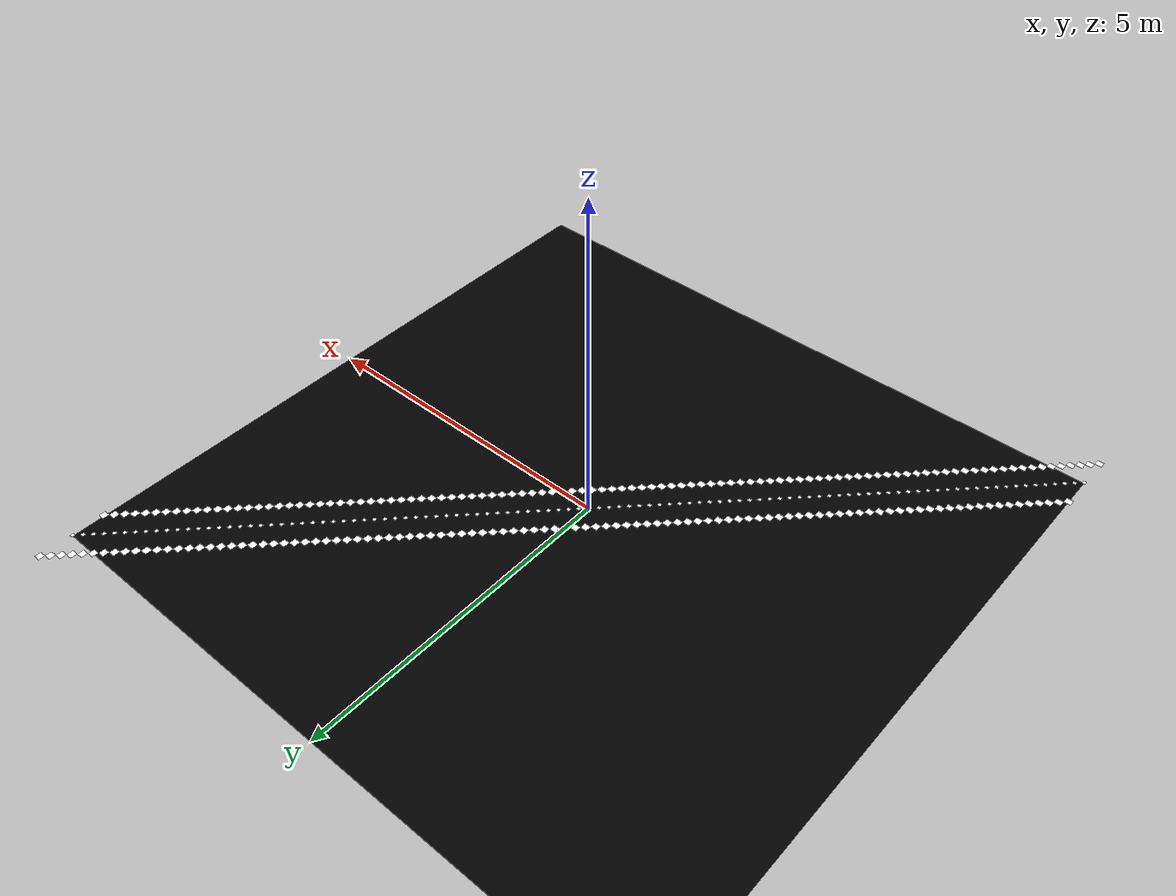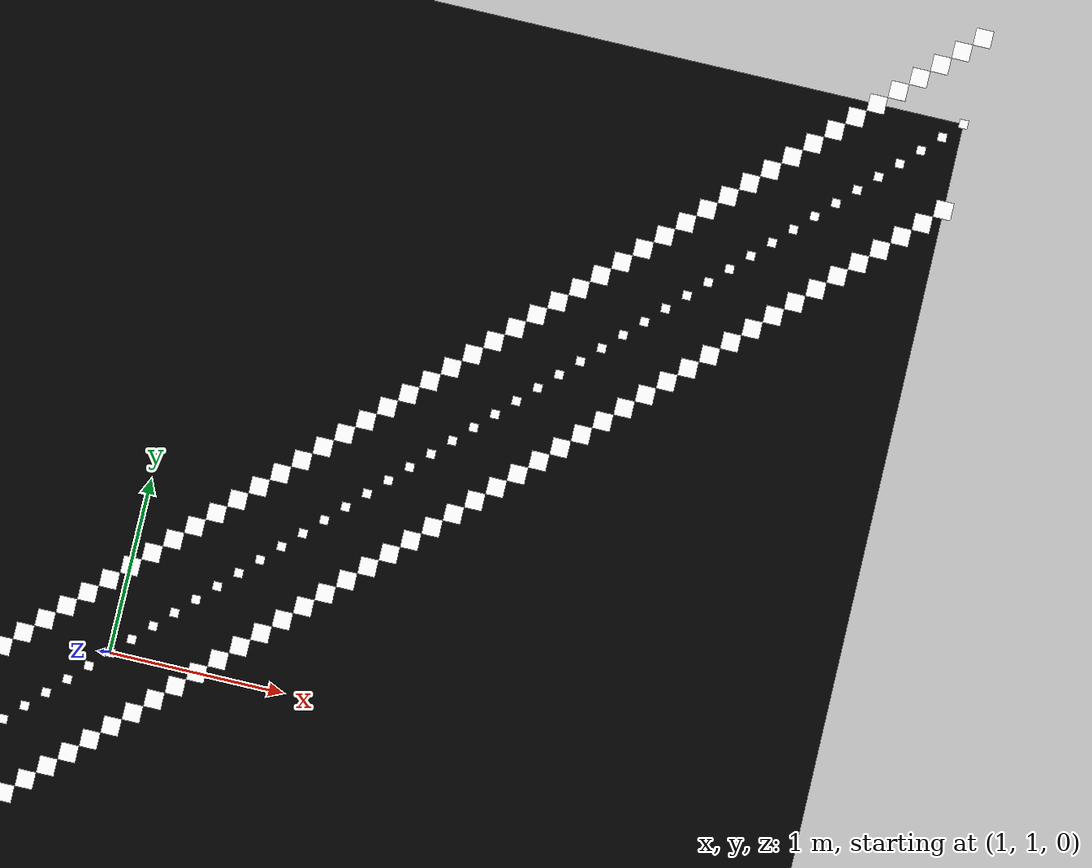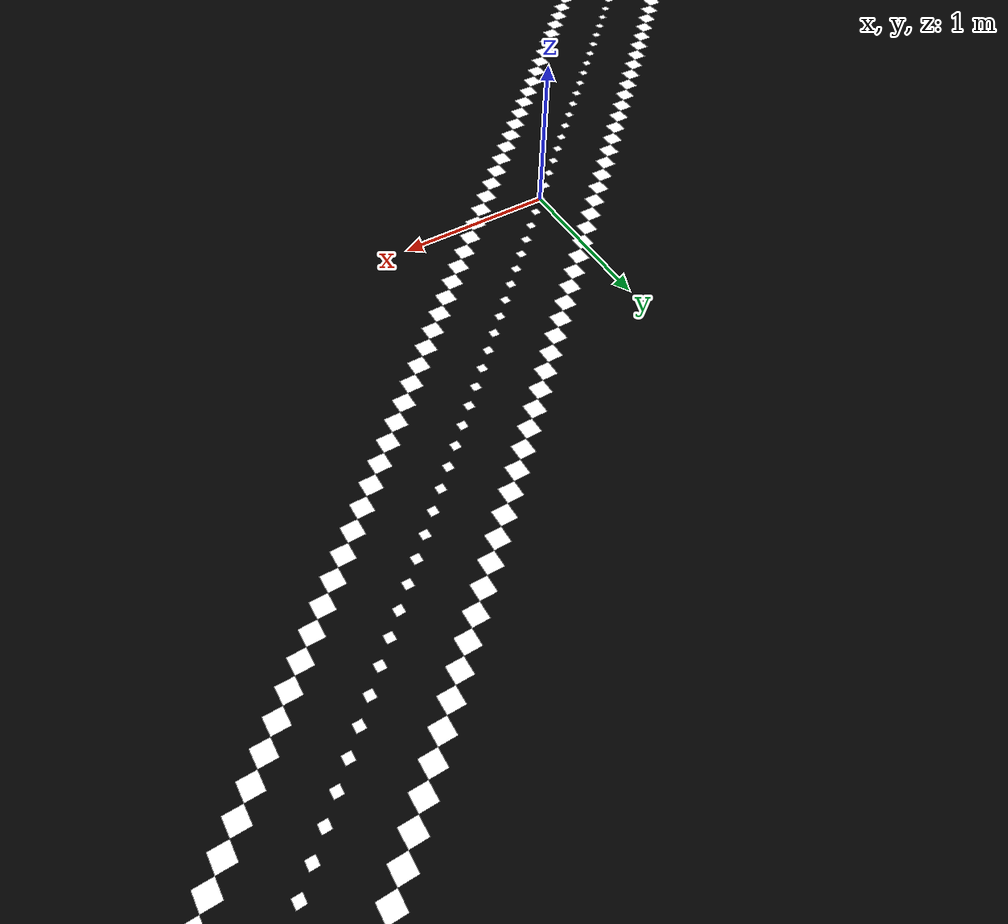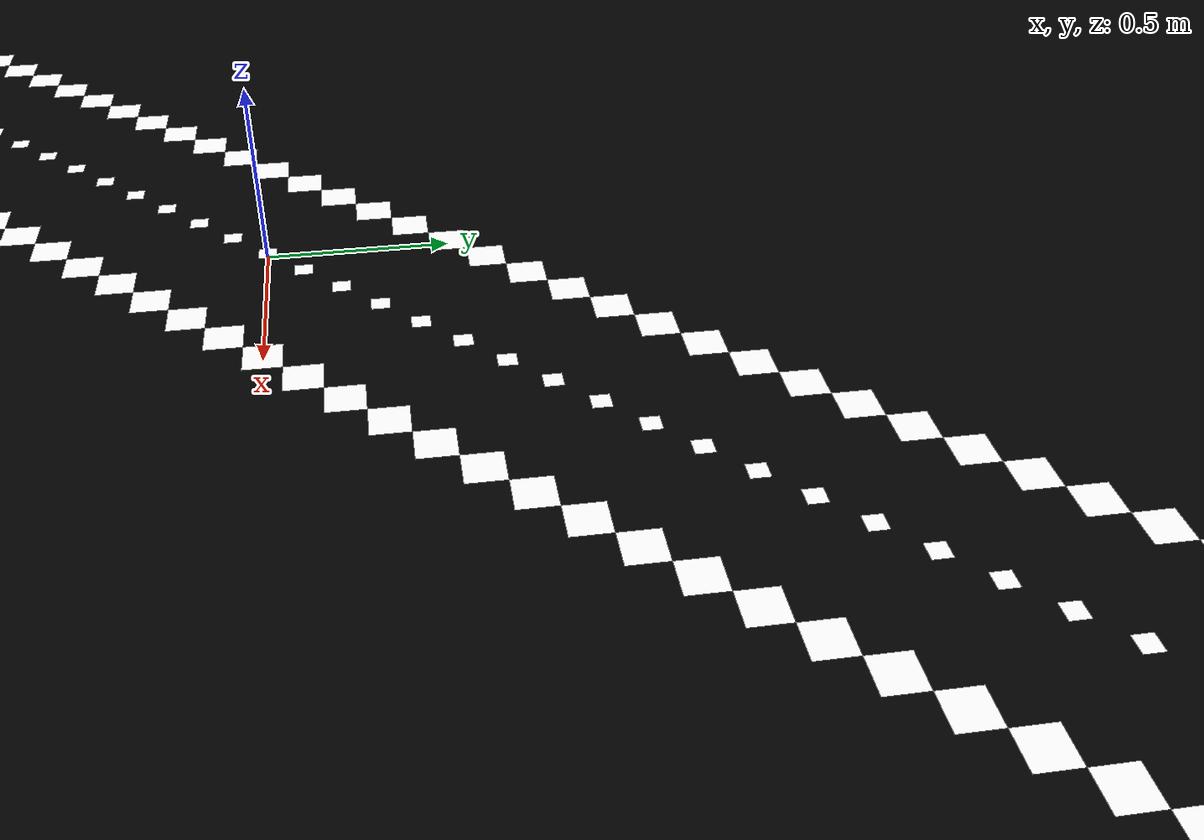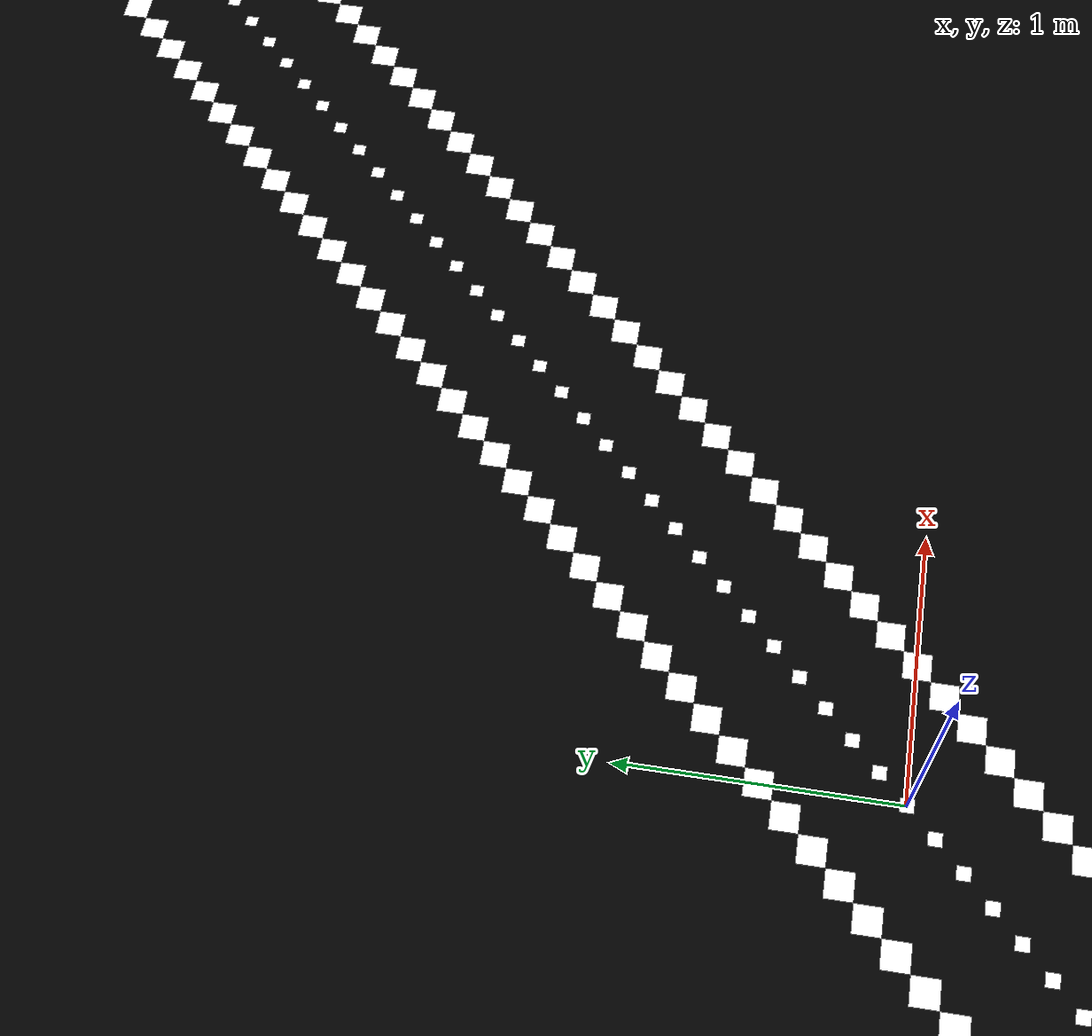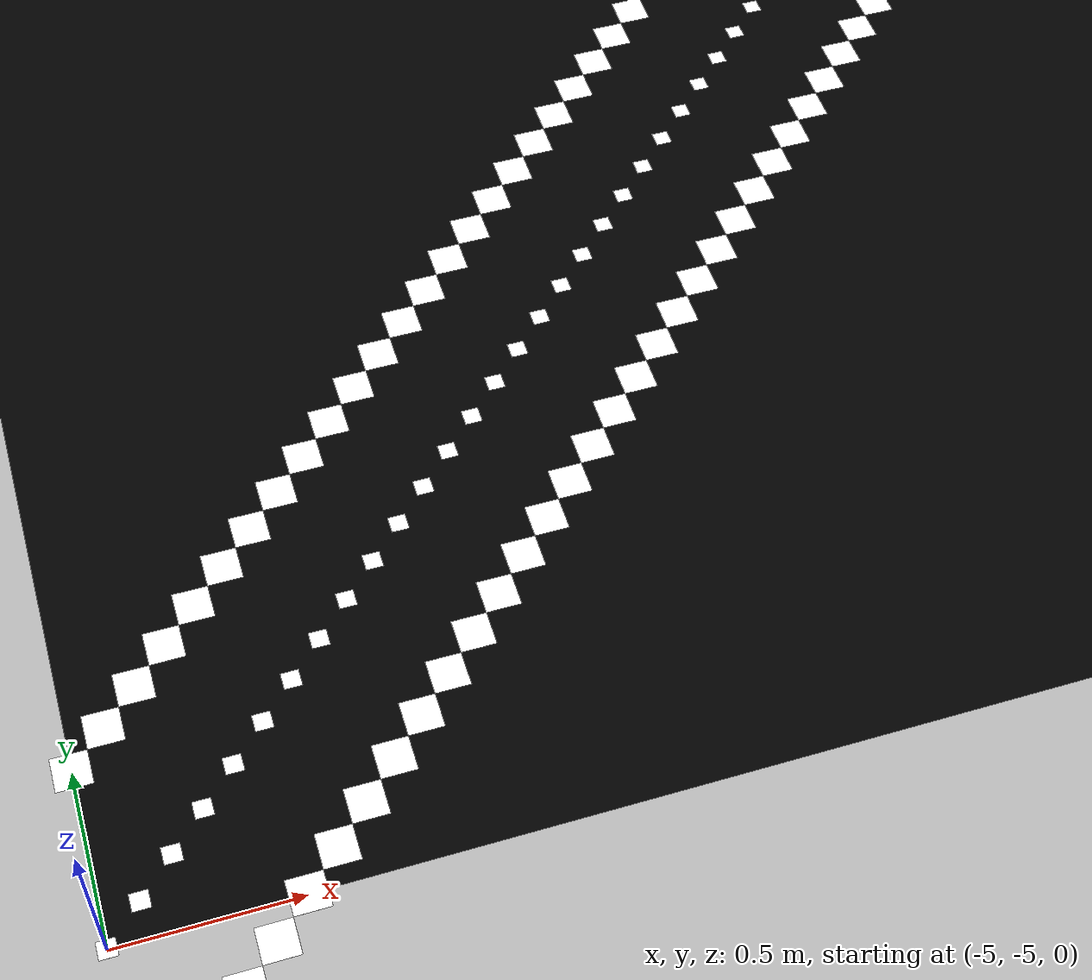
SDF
<?xml version='1.0'?>
<sdf version='1.5'>
  <model name='AutoNOMOS_mini_intersection'>
    <static>true</static>
    <link name="field">
      <pose>0 0 0.01 0 0 0</pose>
      <collision name="collision">
        <geometry>
          <plane>
            <normal>0 0 1</normal>
            <size>10 10</size>
          </plane>
        </geometry>
        <surface>
          <friction>
            <ode>
              <mu>100</mu>
              <mu2>50</mu2>
            </ode>
          </friction>
        </surface>
      </collision>
      <visual name="carpet">
        <cast_shadows>false</cast_shadows>
        <geometry>
          <plane>
            <normal>0 0 1</normal>
            <size>10 10</size>
          </plane>
        </geometry>
        <material>
          <ambient>0 0 0 0</ambient>
          <diffuse>0 0 0 1</diffuse>
          <specular>0 0 0 0</specular>
          <emissive>0 0 0 0</emissive>
        </material>
      </visual>
    </link>

    <link name='L1_p1'>
          <pose>-5 -5 0.011 0 0 0</pose>
            <visual name='visual_L1_p1'>
             <cast_shadows>false</cast_shadows>
            <geometry>
          <plane>
            <normal>0 0 1</normal>
            <size>.05 .05</size>
          </plane>
        </geometry>
          <material>
          <ambient>0 0 0 0</ambient>
          <diffuse>1 1 1 0</diffuse>
          <specular>0 0 0 0</specular>
          <emissive>0 0 0 0</emissive>
        </material>
      </visual>
       </link>
          <!-- ####################### NEW LINE ####################### -->
          <link name='L2_p1'>
          <pose>-5 -4.5 0.011 0 0 0</pose>
            <visual name='visual_L2_p1'>
             <cast_shadows>false</cast_shadows>
            <geometry>
          <plane>
            <normal>0 0 1</normal>
            <size>.1 .1</size>
          </plane>
        </geometry>
          <material>
          <ambient>0 0 0 0</ambient>
          <diffuse>1 1 1 0</diffuse>
          <specular>0 0 0 0</specular>
          <emissive>0 0 0 0</emissive>
        </material>
      </visual>
       </link>
          <!-- ####################### NEW LINE ####################### -->
          <link name='L3_p1'>
          <pose>-5 -5.5 0.011 0 0 0</pose>
            <visual name='visual_L3_p1'>
             <cast_shadows>false</cast_shadows>
            <geometry>
          <plane>
            <normal>0 0 1</normal>
            <size>.1 .1</size>
          </plane>
        </geometry>
          <material>
          <ambient>0 0 0 0</ambient>
          <diffuse>1 1 1 0</diffuse>
          <specular>0 0 0 0</specular>
          <emissive>0 0 0 0</emissive>
        </material>
      </visual>
       </link>
          <!-- ####################### NEW LINE ####################### -->
<link name='L1_p2'>
          <pose>-4.9 -4.9 0.011 0 0 0</pose>
            <visual name='visual_L1_p2'>
             <cast_shadows>false</cast_shadows>
            <geometry>
          <plane>
            <normal>0 0 1</normal>
            <size>.05 .05</size>
          </plane>
        </geometry>
          <material>
          <ambient>0 0 0 0</ambient>
          <diffuse>1 1 1 0</diffuse>
          <specular>0 0 0 0</specular>
          <emissive>0 0 0 0</emissive>
        </material>
      </visual>
       </link>
          <!-- ####################### NEW LINE ####################### -->
          <link name='L2_p2'>
          <pose>-4.9 -4.4 0.011 0 0 0</pose>
            <visual name='visual_L2_p2'>
             <cast_shadows>false</cast_shadows>
            <geometry>
          <plane>
            <normal>0 0 1</normal>
            <size>.1 .1</size>
          </plane>
        </geometry>
          <material>
          <ambient>0 0 0 0</ambient>
          <diffuse>1 1 1 0</diffuse>
          <specular>0 0 0 0</specular>
          <emissive>0 0 0 0</emissive>
        </material>
      </visual>
       </link>
          <!-- ####################### NEW LINE ####################### -->
          <link name='L3_p2'>
          <pose>-4.9 -5.4 0.011 0 0 0</pose>
            <visual name='visual_L3_p2'>
             <cast_shadows>false</cast_shadows>
            <geometry>
          <plane>
            <normal>0 0 1</normal>
            <size>.1 .1</size>
          </plane>
        </geometry>
          <material>
          <ambient>0 0 0 0</ambient>
          <diffuse>1 1 1 0</diffuse>
          <specular>0 0 0 0</specular>
          <emissive>0 0 0 0</emissive>
        </material>
      </visual>
       </link>
<link name='L1_p3'>
          <pose>-4.8 -4.8 0.011 0 0 0</pose>
            <visual name='visual_L1_p3'>
             <cast_shadows>false</cast_shadows>
            <geometry>
          <plane>
            <normal>0 0 1</normal>
            <size>.05 .05</size>
          </plane>
        </geometry>
          <material>
          <ambient>0 0 0 0</ambient>
          <diffuse>1 1 1 0</diffuse>
          <specular>0 0 0 0</specular>
          <emissive>0 0 0 0</emissive>
        </material>
      </visual>
       </link>
          <!-- ####################### NEW LINE ####################### -->
          <link name='L2_p3'>
          <pose>-4.8 -4.3 0.011 0 0 0</pose>
            <visual name='visual_L2_p3'>
             <cast_shadows>false</cast_shadows>
            <geometry>
          <plane>
            <normal>0 0 1</normal>
            <size>.1 .1</size>
          </plane>
        </geometry>
          <material>
          <ambient>0 0 0 0</ambient>
          <diffuse>1 1 1 0</diffuse>
          <specular>0 0 0 0</specular>
          <emissive>0 0 0 0</emissive>
        </material>
      </visual>
       </link>
          <!-- ####################### NEW LINE ####################### -->
          <link name='L3_p3'>
          <pose>-4.8 -5.3 0.011 0 0 0</pose>
            <visual name='visual_L3_p3'>
             <cast_shadows>false</cast_shadows>
            <geometry>
          <plane>
            <normal>0 0 1</normal>
            <size>.1 .1</size>
          </plane>
        </geometry>
          <material>
          <ambient>0 0 0 0</ambient>
          <diffuse>1 1 1 0</diffuse>
          <specular>0 0 0 0</specular>
          <emissive>0 0 0 0</emissive>
        </material>
      </visual>
       </link>
<link name='L1_p4'>
          <pose>-4.7 -4.7 0.011 0 0 0</pose>
            <visual name='visual_L1_p4'>
             <cast_shadows>false</cast_shadows>
            <geometry>
          <plane>
            <normal>0 0 1</normal>
            <size>.05 .05</size>
          </plane>
        </geometry>
          <material>
          <ambient>0 0 0 0</ambient>
          <diffuse>1 1 1 0</diffuse>
          <specular>0 0 0 0</specular>
          <emissive>0 0 0 0</emissive>
        </material>
      </visual>
       </link>
          <!-- ####################### NEW LINE ####################### -->
          <link name='L2_p4'>
          <pose>-4.7 -4.2 0.011 0 0 0</pose>
            <visual name='visual_L2_p4'>
             <cast_shadows>false</cast_shadows>
            <geometry>
          <plane>
            <normal>0 0 1</normal>
            <size>.1 .1</size>
          </plane>
        </geometry>
          <material>
          <ambient>0 0 0 0</ambient>
          <diffuse>1 1 1 0</diffuse>
          <specular>0 0 0 0</specular>
          <emissive>0 0 0 0</emissive>
        </material>
      </visual>
       </link>
          <!-- ####################### NEW LINE ####################### -->
          <link name='L3_p4'>
          <pose>-4.7 -5.2 0.011 0 0 0</pose>
            <visual name='visual_L3_p4'>
             <cast_shadows>false</cast_shadows>
            <geometry>
          <plane>
            <normal>0 0 1</normal>
            <size>.1 .1</size>
          </plane>
        </geometry>
          <material>
          <ambient>0 0 0 0</ambient>
          <diffuse>1 1 1 0</diffuse>
          <specular>0 0 0 0</specular>
          <emissive>0 0 0 0</emissive>
        </material>
      </visual>
       </link>
<link name='L1_p5'>
          <pose>-4.6 -4.6 0.011 0 0 0</pose>
            <visual name='visual_L1_p5'>
             <cast_shadows>false</cast_shadows>
            <geometry>
          <plane>
            <normal>0 0 1</normal>
            <size>.05 .05</size>
          </plane>
        </geometry>
          <material>
          <ambient>0 0 0 0</ambient>
          <diffuse>1 1 1 0</diffuse>
          <specular>0 0 0 0</specular>
          <emissive>0 0 0 0</emissive>
        </material>
      </visual>
       </link>
          <!-- ####################### NEW LINE ####################### -->
          <link name='L2_p5'>
          <pose>-4.6 -4.1 0.011 0 0 0</pose>
            <visual name='visual_L2_p5'>
             <cast_shadows>false</cast_shadows>
            <geometry>
          <plane>
            <normal>0 0 1</normal>
            <size>.1 .1</size>
          </plane>
        </geometry>
          <material>
          <ambient>0 0 0 0</ambient>
          <diffuse>1 1 1 0</diffuse>
          <specular>0 0 0 0</specular>
          <emissive>0 0 0 0</emissive>
        </material>
      </visual>
       </link>
          <!-- ####################### NEW LINE ####################### -->
          <link name='L3_p5'>
          <pose>-4.6 -5.1 0.011 0 0 0</pose>
            <visual name='visual_L3_p5'>
             <cast_shadows>false</cast_shadows>
            <geometry>
          <plane>
            <normal>0 0 1</normal>
            <size>.1 .1</size>
          </plane>
        </geometry>
          <material>
          <ambient>0 0 0 0</ambient>
          <diffuse>1 1 1 0</diffuse>
          <specular>0 0 0 0</specular>
          <emissive>0 0 0 0</emissive>
        </material>
      </visual>
       </link>
<link name='L1_p6'>
          <pose>-4.5 -4.5 0.011 0 0 0</pose>
            <visual name='visual_L1_p6'>
             <cast_shadows>false</cast_shadows>
            <geometry>
          <plane>
            <normal>0 0 1</normal>
            <size>.05 .05</size>
          </plane>
        </geometry>
          <material>
          <ambient>0 0 0 0</ambient>
          <diffuse>1 1 1 0</diffuse>
          <specular>0 0 0 0</specular>
          <emissive>0 0 0 0</emissive>
        </material>
      </visual>
       </link>
          <!-- ####################### NEW LINE ####################### -->
          <link name='L2_p6'>
          <pose>-4.5 -4 0.011 0 0 0</pose>
            <visual name='visual_L2_p6'>
             <cast_shadows>false</cast_shadows>
            <geometry>
          <plane>
            <normal>0 0 1</normal>
            <size>.1 .1</size>
          </plane>
        </geometry>
          <material>
          <ambient>0 0 0 0</ambient>
          <diffuse>1 1 1 0</diffuse>
          <specular>0 0 0 0</specular>
          <emissive>0 0 0 0</emissive>
        </material>
      </visual>
       </link>
          <!-- ####################### NEW LINE ####################### -->
          <link name='L3_p6'>
          <pose>-4.5 -5 0.011 0 0 0</pose>
            <visual name='visual_L3_p6'>
             <cast_shadows>false</cast_shadows>
            <geometry>
          <plane>
            <normal>0 0 1</normal>
            <size>.1 .1</size>
          </plane>
        </geometry>
          <material>
          <ambient>0 0 0 0</ambient>
          <diffuse>1 1 1 0</diffuse>
          <specular>0 0 0 0</specular>
          <emissive>0 0 0 0</emissive>
        </material>
      </visual>
       </link>
<link name='L1_p7'>
          <pose>-4.4 -4.4 0.011 0 0 0</pose>
            <visual name='visual_L1_p7'>
             <cast_shadows>false</cast_shadows>
            <geometry>
          <plane>
            <normal>0 0 1</normal>
            <size>.05 .05</size>
          </plane>
        </geometry>
          <material>
          <ambient>0 0 0 0</ambient>
          <diffuse>1 1 1 0</diffuse>
          <specular>0 0 0 0</specular>
          <emissive>0 0 0 0</emissive>
        </material>
      </visual>
       </link>
          <!-- ####################### NEW LINE ####################### -->
          <link name='L2_p7'>
          <pose>-4.4 -3.9 0.011 0 0 0</pose>
            <visual name='visual_L2_p7'>
             <cast_shadows>false</cast_shadows>
            <geometry>
          <plane>
            <normal>0 0 1</normal>
            <size>.1 .1</size>
          </plane>
        </geometry>
          <material>
          <ambient>0 0 0 0</ambient>
          <diffuse>1 1 1 0</diffuse>
          <specular>0 0 0 0</specular>
          <emissive>0 0 0 0</emissive>
        </material>
      </visual>
       </link>
          <!-- ####################### NEW LINE ####################### -->
          <link name='L3_p7'>
          <pose>-4.4 -4.9 0.011 0 0 0</pose>
            <visual name='visual_L3_p7'>
             <cast_shadows>false</cast_shadows>
            <geometry>
          <plane>
            <normal>0 0 1</normal>
            <size>.1 .1</size>
          </plane>
        </geometry>
          <material>
          <ambient>0 0 0 0</ambient>
          <diffuse>1 1 1 0</diffuse>
          <specular>0 0 0 0</specular>
          <emissive>0 0 0 0</emissive>
        </material>
      </visual>
       </link>
<link name='L1_p8'>
          <pose>-4.3 -4.3 0.011 0 0 0</pose>
            <visual name='visual_L1_p8'>
             <cast_shadows>false</cast_shadows>
            <geometry>
          <plane>
            <normal>0 0 1</normal>
            <size>.05 .05</size>
          </plane>
        </geometry>
          <material>
          <ambient>0 0 0 0</ambient>
          <diffuse>1 1 1 0</diffuse>
          <specular>0 0 0 0</specular>
          <emissive>0 0 0 0</emissive>
        </material>
      </visual>
       </link>
          <!-- ####################### NEW LINE ####################### -->
          <link name='L2_p8'>
          <pose>-4.3 -3.8 0.011 0 0 0</pose>
            <visual name='visual_L2_p8'>
             <cast_shadows>false</cast_shadows>
            <geometry>
          <plane>
            <normal>0 0 1</normal>
            <size>.1 .1</size>
          </plane>
        </geometry>
          <material>
          <ambient>0 0 0 0</ambient>
          <diffuse>1 1 1 0</diffuse>
          <specular>0 0 0 0</specular>
          <emissive>0 0 0 0</emissive>
        </material>
      </visual>
       </link>
          <!-- ####################### NEW LINE ####################### -->
          <link name='L3_p8'>
          <pose>-4.3 -4.8 0.011 0 0 0</pose>
            <visual name='visual_L3_p8'>
             <cast_shadows>false</cast_shadows>
            <geometry>
          <plane>
            <normal>0 0 1</normal>
            <size>.1 .1</size>
          </plane>
        </geometry>
          <material>
          <ambient>0 0 0 0</ambient>
          <diffuse>1 1 1 0</diffuse>
          <specular>0 0 0 0</specular>
          <emissive>0 0 0 0</emissive>
        </material>
      </visual>
       </link>
<link name='L1_p9'>
          <pose>-4.2 -4.2 0.011 0 0 0</pose>
            <visual name='visual_L1_p9'>
             <cast_shadows>false</cast_shadows>
            <geometry>
          <plane>
            <normal>0 0 1</normal>
            <size>.05 .05</size>
          </plane>
        </geometry>
          <material>
          <ambient>0 0 0 0</ambient>
          <diffuse>1 1 1 0</diffuse>
          <specular>0 0 0 0</specular>
          <emissive>0 0 0 0</emissive>
        </material>
      </visual>
       </link>
          <!-- ####################### NEW LINE ####################### -->
          <link name='L2_p9'>
          <pose>-4.2 -3.7 0.011 0 0 0</pose>
            <visual name='visual_L2_p9'>
             <cast_shadows>false</cast_shadows>
            <geometry>
          <plane>
            <normal>0 0 1</normal>
            <size>.1 .1</size>
          </plane>
        </geometry>
          <material>
          <ambient>0 0 0 0</ambient>
          <diffuse>1 1 1 0</diffuse>
          <specular>0 0 0 0</specular>
          <emissive>0 0 0 0</emissive>
        </material>
      </visual>
       </link>
          <!-- ####################### NEW LINE ####################### -->
          <link name='L3_p9'>
          <pose>-4.2 -4.7 0.011 0 0 0</pose>
            <visual name='visual_L3_p9'>
             <cast_shadows>false</cast_shadows>
            <geometry>
          <plane>
            <normal>0 0 1</normal>
            <size>.1 .1</size>
          </plane>
        </geometry>
          <material>
          <ambient>0 0 0 0</ambient>
          <diffuse>1 1 1 0</diffuse>
          <specular>0 0 0 0</specular>
          <emissive>0 0 0 0</emissive>
        </material>
      </visual>
       </link>
<link name='L1_p10'>
          <pose>-4.1 -4.1 0.011 0 0 0</pose>
            <visual name='visual_L1_p10'>
             <cast_shadows>false</cast_shadows>
            <geometry>
          <plane>
            <normal>0 0 1</normal>
            <size>.05 .05</size>
          </plane>
        </geometry>
          <material>
          <ambient>0 0 0 0</ambient>
          <diffuse>1 1 1 0</diffuse>
          <specular>0 0 0 0</specular>
          <emissive>0 0 0 0</emissive>
        </material>
      </visual>
       </link>
          <!-- ####################### NEW LINE ####################### -->
          <link name='L2_p10'>
          <pose>-4.1 -3.6 0.011 0 0 0</pose>
            <visual name='visual_L2_p10'>
             <cast_shadows>false</cast_shadows>
            <geometry>
          <plane>
            <normal>0 0 1</normal>
            <size>.1 .1</size>
          </plane>
        </geometry>
          <material>
          <ambient>0 0 0 0</ambient>
          <diffuse>1 1 1 0</diffuse>
          <specular>0 0 0 0</specular>
          <emissive>0 0 0 0</emissive>
        </material>
      </visual>
       </link>
          <!-- ####################### NEW LINE ####################### -->
          <link name='L3_p10'>
          <pose>-4.1 -4.6 0.011 0 0 0</pose>
            <visual name='visual_L3_p10'>
             <cast_shadows>false</cast_shadows>
            <geometry>
          <plane>
            <normal>0 0 1</normal>
            <size>.1 .1</size>
          </plane>
        </geometry>
          <material>
          <ambient>0 0 0 0</ambient>
          <diffuse>1 1 1 0</diffuse>
          <specular>0 0 0 0</specular>
          <emissive>0 0 0 0</emissive>
        </material>
      </visual>
       </link>
<link name='L1_p11'>
          <pose>-4 -4 0.011 0 0 0</pose>
            <visual name='visual_L1_p11'>
             <cast_shadows>false</cast_shadows>
            <geometry>
          <plane>
            <normal>0 0 1</normal>
            <size>.05 .05</size>
          </plane>
        </geometry>
          <material>
          <ambient>0 0 0 0</ambient>
          <diffuse>1 1 1 0</diffuse>
          <specular>0 0 0 0</specular>
          <emissive>0 0 0 0</emissive>
        </material>
      </visual>
       </link>
          <!-- ####################### NEW LINE ####################### -->
          <link name='L2_p11'>
          <pose>-4 -3.5 0.011 0 0 0</pose>
            <visual name='visual_L2_p11'>
             <cast_shadows>false</cast_shadows>
            <geometry>
          <plane>
            <normal>0 0 1</normal>
            <size>.1 .1</size>
          </plane>
        </geometry>
          <material>
          <ambient>0 0 0 0</ambient>
          <diffuse>1 1 1 0</diffuse>
          <specular>0 0 0 0</specular>
          <emissive>0 0 0 0</emissive>
        </material>
      </visual>
       </link>
          <!-- ####################### NEW LINE ####################### -->
          <link name='L3_p11'>
          <pose>-4 -4.5 0.011 0 0 0</pose>
            <visual name='visual_L3_p11'>
             <cast_shadows>false</cast_shadows>
            <geometry>
          <plane>
            <normal>0 0 1</normal>
            <size>.1 .1</size>
          </plane>
        </geometry>
          <material>
          <ambient>0 0 0 0</ambient>
          <diffuse>1 1 1 0</diffuse>
          <specular>0 0 0 0</specular>
          <emissive>0 0 0 0</emissive>
        </material>
      </visual>
       </link>
<link name='L1_p12'>
          <pose>-3.9 -3.9 0.011 0 0 0</pose>
            <visual name='visual_L1_p12'>
             <cast_shadows>false</cast_shadows>
            <geometry>
          <plane>
            <normal>0 0 1</normal>
            <size>.05 .05</size>
          </plane>
        </geometry>
          <material>
          <ambient>0 0 0 0</ambient>
          <diffuse>1 1 1 0</diffuse>
          <specular>0 0 0 0</specular>
          <emissive>0 0 0 0</emissive>
        </material>
      </visual>
       </link>
          <!-- ####################### NEW LINE ####################### -->
          <link name='L2_p12'>
          <pose>-3.9 -3.4 0.011 0 0 0</pose>
            <visual name='visual_L2_p12'>
             <cast_shadows>false</cast_shadows>
            <geometry>
          <plane>
            <normal>0 0 1</normal>
            <size>.1 .1</size>
          </plane>
        </geometry>
          <material>
          <ambient>0 0 0 0</ambient>
          <diffuse>1 1 1 0</diffuse>
          <specular>0 0 0 0</specular>
          <emissive>0 0 0 0</emissive>
        </material>
      </visual>
       </link>
          <!-- ####################### NEW LINE ####################### -->
          <link name='L3_p12'>
          <pose>-3.9 -4.4 0.011 0 0 0</pose>
            <visual name='visual_L3_p12'>
             <cast_shadows>false</cast_shadows>
            <geometry>
          <plane>
            <normal>0 0 1</normal>
            <size>.1 .1</size>
          </plane>
        </geometry>
          <material>
          <ambient>0 0 0 0</ambient>
          <diffuse>1 1 1 0</diffuse>
          <specular>0 0 0 0</specular>
          <emissive>0 0 0 0</emissive>
        </material>
      </visual>
       </link>
<link name='L1_p13'>
          <pose>-3.8 -3.8 0.011 0 0 0</pose>
            <visual name='visual_L1_p13'>
             <cast_shadows>false</cast_shadows>
            <geometry>
          <plane>
            <normal>0 0 1</normal>
            <size>.05 .05</size>
          </plane>
        </geometry>
          <material>
          <ambient>0 0 0 0</ambient>
          <diffuse>1 1 1 0</diffuse>
          <specular>0 0 0 0</specular>
          <emissive>0 0 0 0</emissive>
        </material>
      </visual>
       </link>
          <!-- ####################### NEW LINE ####################### -->
          <link name='L2_p13'>
          <pose>-3.8 -3.3 0.011 0 0 0</pose>
            <visual name='visual_L2_p13'>
             <cast_shadows>false</cast_shadows>
            <geometry>
          <plane>
            <normal>0 0 1</normal>
            <size>.1 .1</size>
          </plane>
        </geometry>
          <material>
          <ambient>0 0 0 0</ambient>
          <diffuse>1 1 1 0</diffuse>
          <specular>0 0 0 0</specular>
          <emissive>0 0 0 0</emissive>
        </material>
      </visual>
       </link>
          <!-- ####################### NEW LINE ####################### -->
          <link name='L3_p13'>
          <pose>-3.8 -4.3 0.011 0 0 0</pose>
            <visual name='visual_L3_p13'>
             <cast_shadows>false</cast_shadows>
            <geometry>
          <plane>
            <normal>0 0 1</normal>
            <size>.1 .1</size>
          </plane>
        </geometry>
          <material>
          <ambient>0 0 0 0</ambient>
          <diffuse>1 1 1 0</diffuse>
          <specular>0 0 0 0</specular>
          <emissive>0 0 0 0</emissive>
        </material>
      </visual>
       </link>
<link name='L1_p14'>
          <pose>-3.7 -3.7 0.011 0 0 0</pose>
            <visual name='visual_L1_p14'>
             <cast_shadows>false</cast_shadows>
            <geometry>
          <plane>
            <normal>0 0 1</normal>
            <size>.05 .05</size>
          </plane>
        </geometry>
          <material>
          <ambient>0 0 0 0</ambient>
          <diffuse>1 1 1 0</diffuse>
          <specular>0 0 0 0</specular>
          <emissive>0 0 0 0</emissive>
        </material>
      </visual>
       </link>
          <!-- ####################### NEW LINE ####################### -->
          <link name='L2_p14'>
          <pose>-3.7 -3.2 0.011 0 0 0</pose>
            <visual name='visual_L2_p14'>
             <cast_shadows>false</cast_shadows>
            <geometry>
          <plane>
            <normal>0 0 1</normal>
            <size>.1 .1</size>
          </plane>
        </geometry>
          <material>
          <ambient>0 0 0 0</ambient>
          <diffuse>1 1 1 0</diffuse>
          <specular>0 0 0 0</specular>
          <emissive>0 0 0 0</emissive>
        </material>
      </visual>
       </link>
          <!-- ####################### NEW LINE ####################### -->
          <link name='L3_p14'>
          <pose>-3.7 -4.2 0.011 0 0 0</pose>
            <visual name='visual_L3_p14'>
             <cast_shadows>false</cast_shadows>
            <geometry>
          <plane>
            <normal>0 0 1</normal>
            <size>.1 .1</size>
          </plane>
        </geometry>
          <material>
          <ambient>0 0 0 0</ambient>
          <diffuse>1 1 1 0</diffuse>
          <specular>0 0 0 0</specular>
          <emissive>0 0 0 0</emissive>
        </material>
      </visual>
       </link>
<link name='L1_p15'>
          <pose>-3.6 -3.6 0.011 0 0 0</pose>
            <visual name='visual_L1_p15'>
             <cast_shadows>false</cast_shadows>
            <geometry>
          <plane>
            <normal>0 0 1</normal>
            <size>.05 .05</size>
          </plane>
        </geometry>
          <material>
          <ambient>0 0 0 0</ambient>
          <diffuse>1 1 1 0</diffuse>
          <specular>0 0 0 0</specular>
          <emissive>0 0 0 0</emissive>
        </material>
      </visual>
       </link>
          <!-- ####################### NEW LINE ####################### -->
          <link name='L2_p15'>
          <pose>-3.6 -3.1 0.011 0 0 0</pose>
            <visual name='visual_L2_p15'>
             <cast_shadows>false</cast_shadows>
            <geometry>
          <plane>
            <normal>0 0 1</normal>
            <size>.1 .1</size>
          </plane>
        </geometry>
          <material>
          <ambient>0 0 0 0</ambient>
          <diffuse>1 1 1 0</diffuse>
          <specular>0 0 0 0</specular>
          <emissive>0 0 0 0</emissive>
        </material>
      </visual>
       </link>
          <!-- ####################### NEW LINE ####################### -->
          <link name='L3_p15'>
          <pose>-3.6 -4.1 0.011 0 0 0</pose>
            <visual name='visual_L3_p15'>
             <cast_shadows>false</cast_shadows>
            <geometry>
          <plane>
            <normal>0 0 1</normal>
            <size>.1 .1</size>
          </plane>
        </geometry>
          <material>
          <ambient>0 0 0 0</ambient>
          <diffuse>1 1 1 0</diffuse>
          <specular>0 0 0 0</specular>
          <emissive>0 0 0 0</emissive>
        </material>
      </visual>
       </link>
<link name='L1_p16'>
          <pose>-3.5 -3.5 0.011 0 0 0</pose>
            <visual name='visual_L1_p16'>
             <cast_shadows>false</cast_shadows>
            <geometry>
          <plane>
            <normal>0 0 1</normal>
            <size>.05 .05</size>
          </plane>
        </geometry>
          <material>
          <ambient>0 0 0 0</ambient>
          <diffuse>1 1 1 0</diffuse>
          <specular>0 0 0 0</specular>
          <emissive>0 0 0 0</emissive>
        </material>
      </visual>
       </link>
          <!-- ####################### NEW LINE ####################### -->
          <link name='L2_p16'>
          <pose>-3.5 -3 0.011 0 0 0</pose>
            <visual name='visual_L2_p16'>
             <cast_shadows>false</cast_shadows>
            <geometry>
          <plane>
            <normal>0 0 1</normal>
            <size>.1 .1</size>
          </plane>
        </geometry>
          <material>
          <ambient>0 0 0 0</ambient>
          <diffuse>1 1 1 0</diffuse>
          <specular>0 0 0 0</specular>
          <emissive>0 0 0 0</emissive>
        </material>
      </visual>
       </link>
          <!-- ####################### NEW LINE ####################### -->
          <link name='L3_p16'>
          <pose>-3.5 -4 0.011 0 0 0</pose>
            <visual name='visual_L3_p16'>
             <cast_shadows>false</cast_shadows>
            <geometry>
          <plane>
            <normal>0 0 1</normal>
            <size>.1 .1</size>
          </plane>
        </geometry>
          <material>
          <ambient>0 0 0 0</ambient>
          <diffuse>1 1 1 0</diffuse>
          <specular>0 0 0 0</specular>
          <emissive>0 0 0 0</emissive>
        </material>
      </visual>
       </link>
<link name='L1_p17'>
          <pose>-3.4 -3.4 0.011 0 0 0</pose>
            <visual name='visual_L1_p17'>
             <cast_shadows>false</cast_shadows>
            <geometry>
          <plane>
            <normal>0 0 1</normal>
            <size>.05 .05</size>
          </plane>
        </geometry>
          <material>
          <ambient>0 0 0 0</ambient>
          <diffuse>1 1 1 0</diffuse>
          <specular>0 0 0 0</specular>
          <emissive>0 0 0 0</emissive>
        </material>
      </visual>
       </link>
          <!-- ####################### NEW LINE ####################### -->
          <link name='L2_p17'>
          <pose>-3.4 -2.9 0.011 0 0 0</pose>
            <visual name='visual_L2_p17'>
             <cast_shadows>false</cast_shadows>
            <geometry>
          <plane>
            <normal>0 0 1</normal>
            <size>.1 .1</size>
          </plane>
        </geometry>
          <material>
          <ambient>0 0 0 0</ambient>
          <diffuse>1 1 1 0</diffuse>
          <specular>0 0 0 0</specular>
          <emissive>0 0 0 0</emissive>
        </material>
      </visual>
       </link>
          <!-- ####################### NEW LINE ####################### -->
          <link name='L3_p17'>
          <pose>-3.4 -3.9 0.011 0 0 0</pose>
            <visual name='visual_L3_p17'>
             <cast_shadows>false</cast_shadows>
            <geometry>
          <plane>
            <normal>0 0 1</normal>
            <size>.1 .1</size>
          </plane>
        </geometry>
          <material>
          <ambient>0 0 0 0</ambient>
          <diffuse>1 1 1 0</diffuse>
          <specular>0 0 0 0</specular>
          <emissive>0 0 0 0</emissive>
        </material>
      </visual>
       </link>
<link name='L1_p18'>
          <pose>-3.3 -3.3 0.011 0 0 0</pose>
            <visual name='visual_L1_p18'>
             <cast_shadows>false</cast_shadows>
            <geometry>
          <plane>
            <normal>0 0 1</normal>
            <size>.05 .05</size>
          </plane>
        </geometry>
          <material>
          <ambient>0 0 0 0</ambient>
          <diffuse>1 1 1 0</diffuse>
          <specular>0 0 0 0</specular>
          <emissive>0 0 0 0</emissive>
        </material>
      </visual>
       </link>
          <!-- ####################### NEW LINE ####################### -->
          <link name='L2_p18'>
          <pose>-3.3 -2.8 0.011 0 0 0</pose>
            <visual name='visual_L2_p18'>
             <cast_shadows>false</cast_shadows>
            <geometry>
          <plane>
            <normal>0 0 1</normal>
            <size>.1 .1</size>
          </plane>
        </geometry>
          <material>
          <ambient>0 0 0 0</ambient>
          <diffuse>1 1 1 0</diffuse>
          <specular>0 0 0 0</specular>
          <emissive>0 0 0 0</emissive>
        </material>
      </visual>
       </link>
          <!-- ####################### NEW LINE ####################### -->
          <link name='L3_p18'>
          <pose>-3.3 -3.8 0.011 0 0 0</pose>
            <visual name='visual_L3_p18'>
             <cast_shadows>false</cast_shadows>
            <geometry>
          <plane>
            <normal>0 0 1</normal>
            <size>.1 .1</size>
          </plane>
        </geometry>
          <material>
          <ambient>0 0 0 0</ambient>
          <diffuse>1 1 1 0</diffuse>
          <specular>0 0 0 0</specular>
          <emissive>0 0 0 0</emissive>
        </material>
      </visual>
       </link>
<link name='L1_p19'>
          <pose>-3.2 -3.2 0.011 0 0 0</pose>
            <visual name='visual_L1_p19'>
             <cast_shadows>false</cast_shadows>
            <geometry>
          <plane>
            <normal>0 0 1</normal>
            <size>.05 .05</size>
          </plane>
        </geometry>
          <material>
          <ambient>0 0 0 0</ambient>
          <diffuse>1 1 1 0</diffuse>
          <specular>0 0 0 0</specular>
          <emissive>0 0 0 0</emissive>
        </material>
      </visual>
       </link>
          <!-- ####################### NEW LINE ####################### -->
          <link name='L2_p19'>
          <pose>-3.2 -2.7 0.011 0 0 0</pose>
            <visual name='visual_L2_p19'>
             <cast_shadows>false</cast_shadows>
            <geometry>
          <plane>
            <normal>0 0 1</normal>
            <size>.1 .1</size>
          </plane>
        </geometry>
          <material>
          <ambient>0 0 0 0</ambient>
          <diffuse>1 1 1 0</diffuse>
          <specular>0 0 0 0</specular>
          <emissive>0 0 0 0</emissive>
        </material>
      </visual>
       </link>
          <!-- ####################### NEW LINE ####################### -->
          <link name='L3_p19'>
          <pose>-3.2 -3.7 0.011 0 0 0</pose>
            <visual name='visual_L3_p19'>
             <cast_shadows>false</cast_shadows>
            <geometry>
          <plane>
            <normal>0 0 1</normal>
            <size>.1 .1</size>
          </plane>
        </geometry>
          <material>
          <ambient>0 0 0 0</ambient>
          <diffuse>1 1 1 0</diffuse>
          <specular>0 0 0 0</specular>
          <emissive>0 0 0 0</emissive>
        </material>
      </visual>
       </link>
<link name='L1_p20'>
          <pose>-3.1 -3.1 0.011 0 0 0</pose>
            <visual name='visual_L1_p20'>
             <cast_shadows>false</cast_shadows>
            <geometry>
          <plane>
            <normal>0 0 1</normal>
            <size>.05 .05</size>
          </plane>
        </geometry>
          <material>
          <ambient>0 0 0 0</ambient>
          <diffuse>1 1 1 0</diffuse>
          <specular>0 0 0 0</specular>
          <emissive>0 0 0 0</emissive>
        </material>
      </visual>
       </link>
          <!-- ####################### NEW LINE ####################### -->
          <link name='L2_p20'>
          <pose>-3.1 -2.6 0.011 0 0 0</pose>
            <visual name='visual_L2_p20'>
             <cast_shadows>false</cast_shadows>
            <geometry>
          <plane>
            <normal>0 0 1</normal>
            <size>.1 .1</size>
          </plane>
        </geometry>
          <material>
          <ambient>0 0 0 0</ambient>
          <diffuse>1 1 1 0</diffuse>
          <specular>0 0 0 0</specular>
          <emissive>0 0 0 0</emissive>
        </material>
      </visual>
       </link>
          <!-- ####################### NEW LINE ####################### -->
          <link name='L3_p20'>
          <pose>-3.1 -3.6 0.011 0 0 0</pose>
            <visual name='visual_L3_p20'>
             <cast_shadows>false</cast_shadows>
            <geometry>
          <plane>
            <normal>0 0 1</normal>
            <size>.1 .1</size>
          </plane>
        </geometry>
          <material>
          <ambient>0 0 0 0</ambient>
          <diffuse>1 1 1 0</diffuse>
          <specular>0 0 0 0</specular>
          <emissive>0 0 0 0</emissive>
        </material>
      </visual>
       </link>
<link name='L1_p21'>
          <pose>-3 -3 0.011 0 0 0</pose>
            <visual name='visual_L1_p21'>
             <cast_shadows>false</cast_shadows>
            <geometry>
          <plane>
            <normal>0 0 1</normal>
            <size>.05 .05</size>
          </plane>
        </geometry>
          <material>
          <ambient>0 0 0 0</ambient>
          <diffuse>1 1 1 0</diffuse>
          <specular>0 0 0 0</specular>
          <emissive>0 0 0 0</emissive>
        </material>
      </visual>
       </link>
          <!-- ####################### NEW LINE ####################### -->
          <link name='L2_p21'>
          <pose>-3 -2.5 0.011 0 0 0</pose>
            <visual name='visual_L2_p21'>
             <cast_shadows>false</cast_shadows>
            <geometry>
          <plane>
            <normal>0 0 1</normal>
            <size>.1 .1</size>
          </plane>
        </geometry>
          <material>
          <ambient>0 0 0 0</ambient>
          <diffuse>1 1 1 0</diffuse>
          <specular>0 0 0 0</specular>
          <emissive>0 0 0 0</emissive>
        </material>
      </visual>
       </link>
          <!-- ####################### NEW LINE ####################### -->
          <link name='L3_p21'>
          <pose>-3 -3.5 0.011 0 0 0</pose>
            <visual name='visual_L3_p21'>
             <cast_shadows>false</cast_shadows>
            <geometry>
          <plane>
            <normal>0 0 1</normal>
            <size>.1 .1</size>
          </plane>
        </geometry>
          <material>
          <ambient>0 0 0 0</ambient>
          <diffuse>1 1 1 0</diffuse>
          <specular>0 0 0 0</specular>
          <emissive>0 0 0 0</emissive>
        </material>
      </visual>
       </link>
<link name='L1_p22'>
          <pose>-2.9 -2.9 0.011 0 0 0</pose>
            <visual name='visual_L1_p22'>
             <cast_shadows>false</cast_shadows>
            <geometry>
          <plane>
            <normal>0 0 1</normal>
            <size>.05 .05</size>
          </plane>
        </geometry>
          <material>
          <ambient>0 0 0 0</ambient>
          <diffuse>1 1 1 0</diffuse>
          <specular>0 0 0 0</specular>
          <emissive>0 0 0 0</emissive>
        </material>
      </visual>
       </link>
          <!-- ####################### NEW LINE ####################### -->
          <link name='L2_p22'>
          <pose>-2.9 -2.4 0.011 0 0 0</pose>
            <visual name='visual_L2_p22'>
             <cast_shadows>false</cast_shadows>
            <geometry>
          <plane>
            <normal>0 0 1</normal>
            <size>.1 .1</size>
          </plane>
        </geometry>
          <material>
          <ambient>0 0 0 0</ambient>
          <diffuse>1 1 1 0</diffuse>
          <specular>0 0 0 0</specular>
          <emissive>0 0 0 0</emissive>
        </material>
      </visual>
       </link>
          <!-- ####################### NEW LINE ####################### -->
          <link name='L3_p22'>
          <pose>-2.9 -3.4 0.011 0 0 0</pose>
            <visual name='visual_L3_p22'>
             <cast_shadows>false</cast_shadows>
            <geometry>
          <plane>
            <normal>0 0 1</normal>
            <size>.1 .1</size>
          </plane>
        </geometry>
          <material>
          <ambient>0 0 0 0</ambient>
          <diffuse>1 1 1 0</diffuse>
          <specular>0 0 0 0</specular>
          <emissive>0 0 0 0</emissive>
        </material>
      </visual>
       </link>
<link name='L1_p23'>
          <pose>-2.8 -2.8 0.011 0 0 0</pose>
            <visual name='visual_L1_p23'>
             <cast_shadows>false</cast_shadows>
            <geometry>
          <plane>
            <normal>0 0 1</normal>
            <size>.05 .05</size>
          </plane>
        </geometry>
          <material>
          <ambient>0 0 0 0</ambient>
          <diffuse>1 1 1 0</diffuse>
          <specular>0 0 0 0</specular>
          <emissive>0 0 0 0</emissive>
        </material>
      </visual>
       </link>
          <!-- ####################### NEW LINE ####################### -->
          <link name='L2_p23'>
          <pose>-2.8 -2.3 0.011 0 0 0</pose>
            <visual name='visual_L2_p23'>
             <cast_shadows>false</cast_shadows>
            <geometry>
          <plane>
            <normal>0 0 1</normal>
            <size>.1 .1</size>
          </plane>
        </geometry>
          <material>
          <ambient>0 0 0 0</ambient>
          <diffuse>1 1 1 0</diffuse>
          <specular>0 0 0 0</specular>
          <emissive>0 0 0 0</emissive>
        </material>
      </visual>
       </link>
          <!-- ####################### NEW LINE ####################### -->
          <link name='L3_p23'>
          <pose>-2.8 -3.3 0.011 0 0 0</pose>
            <visual name='visual_L3_p23'>
             <cast_shadows>false</cast_shadows>
            <geometry>
          <plane>
            <normal>0 0 1</normal>
            <size>.1 .1</size>
          </plane>
        </geometry>
          <material>
          <ambient>0 0 0 0</ambient>
          <diffuse>1 1 1 0</diffuse>
          <specular>0 0 0 0</specular>
          <emissive>0 0 0 0</emissive>
        </material>
      </visual>
       </link>
<link name='L1_p24'>
          <pose>-2.7 -2.7 0.011 0 0 0</pose>
            <visual name='visual_L1_p24'>
             <cast_shadows>false</cast_shadows>
            <geometry>
          <plane>
            <normal>0 0 1</normal>
            <size>.05 .05</size>
          </plane>
        </geometry>
          <material>
          <ambient>0 0 0 0</ambient>
          <diffuse>1 1 1 0</diffuse>
          <specular>0 0 0 0</specular>
          <emissive>0 0 0 0</emissive>
        </material>
      </visual>
       </link>
          <!-- ####################### NEW LINE ####################### -->
          <link name='L2_p24'>
          <pose>-2.7 -2.2 0.011 0 0 0</pose>
            <visual name='visual_L2_p24'>
             <cast_shadows>false</cast_shadows>
            <geometry>
          <plane>
            <normal>0 0 1</normal>
            <size>.1 .1</size>
          </plane>
        </geometry>
          <material>
          <ambient>0 0 0 0</ambient>
          <diffuse>1 1 1 0</diffuse>
          <specular>0 0 0 0</specular>
          <emissive>0 0 0 0</emissive>
        </material>
      </visual>
       </link>
          <!-- ####################### NEW LINE ####################### -->
          <link name='L3_p24'>
          <pose>-2.7 -3.2 0.011 0 0 0</pose>
            <visual name='visual_L3_p24'>
             <cast_shadows>false</cast_shadows>
            <geometry>
          <plane>
            <normal>0 0 1</normal>
            <size>.1 .1</size>
          </plane>
        </geometry>
          <material>
          <ambient>0 0 0 0</ambient>
          <diffuse>1 1 1 0</diffuse>
          <specular>0 0 0 0</specular>
          <emissive>0 0 0 0</emissive>
        </material>
      </visual>
       </link>
<link name='L1_p25'>
          <pose>-2.6 -2.6 0.011 0 0 0</pose>
            <visual name='visual_L1_p25'>
             <cast_shadows>false</cast_shadows>
            <geometry>
          <plane>
            <normal>0 0 1</normal>
            <size>.05 .05</size>
          </plane>
        </geometry>
          <material>
          <ambient>0 0 0 0</ambient>
          <diffuse>1 1 1 0</diffuse>
          <specular>0 0 0 0</specular>
          <emissive>0 0 0 0</emissive>
        </material>
      </visual>
       </link>
          <!-- ####################### NEW LINE ####################### -->
          <link name='L2_p25'>
          <pose>-2.6 -2.1 0.011 0 0 0</pose>
            <visual name='visual_L2_p25'>
             <cast_shadows>false</cast_shadows>
            <geometry>
          <plane>
            <normal>0 0 1</normal>
            <size>.1 .1</size>
          </plane>
        </geometry>
          <material>
          <ambient>0 0 0 0</ambient>
          <diffuse>1 1 1 0</diffuse>
          <specular>0 0 0 0</specular>
          <emissive>0 0 0 0</emissive>
        </material>
      </visual>
       </link>
          <!-- ####################### NEW LINE ####################### -->
          <link name='L3_p25'>
          <pose>-2.6 -3.1 0.011 0 0 0</pose>
            <visual name='visual_L3_p25'>
             <cast_shadows>false</cast_shadows>
            <geometry>
          <plane>
            <normal>0 0 1</normal>
            <size>.1 .1</size>
          </plane>
        </geometry>
          <material>
          <ambient>0 0 0 0</ambient>
          <diffuse>1 1 1 0</diffuse>
          <specular>0 0 0 0</specular>
          <emissive>0 0 0 0</emissive>
        </material>
      </visual>
       </link>
<link name='L1_p26'>
          <pose>-2.5 -2.5 0.011 0 0 0</pose>
            <visual name='visual_L1_p26'>
             <cast_shadows>false</cast_shadows>
            <geometry>
          <plane>
            <normal>0 0 1</normal>
            <size>.05 .05</size>
          </plane>
        </geometry>
          <material>
          <ambient>0 0 0 0</ambient>
          <diffuse>1 1 1 0</diffuse>
          <specular>0 0 0 0</specular>
          <emissive>0 0 0 0</emissive>
        </material>
      </visual>
       </link>
          <!-- ####################### NEW LINE ####################### -->
          <link name='L2_p26'>
          <pose>-2.5 -2 0.011 0 0 0</pose>
            <visual name='visual_L2_p26'>
             <cast_shadows>false</cast_shadows>
            <geometry>
          <plane>
            <normal>0 0 1</normal>
            <size>.1 .1</size>
          </plane>
        </geometry>
          <material>
          <ambient>0 0 0 0</ambient>
          <diffuse>1 1 1 0</diffuse>
          <specular>0 0 0 0</specular>
          <emissive>0 0 0 0</emissive>
        </material>
      </visual>
       </link>
          <!-- ####################### NEW LINE ####################### -->
          <link name='L3_p26'>
          <pose>-2.5 -3 0.011 0 0 0</pose>
            <visual name='visual_L3_p26'>
             <cast_shadows>false</cast_shadows>
            <geometry>
          <plane>
            <normal>0 0 1</normal>
            <size>.1 .1</size>
          </plane>
        </geometry>
          <material>
          <ambient>0 0 0 0</ambient>
          <diffuse>1 1 1 0</diffuse>
          <specular>0 0 0 0</specular>
          <emissive>0 0 0 0</emissive>
        </material>
      </visual>
       </link>
<link name='L1_p27'>
          <pose>-2.4 -2.4 0.011 0 0 0</pose>
            <visual name='visual_L1_p27'>
             <cast_shadows>false</cast_shadows>
            <geometry>
          <plane>
            <normal>0 0 1</normal>
            <size>.05 .05</size>
          </plane>
        </geometry>
          <material>
          <ambient>0 0 0 0</ambient>
          <diffuse>1 1 1 0</diffuse>
          <specular>0 0 0 0</specular>
          <emissive>0 0 0 0</emissive>
        </material>
      </visual>
       </link>
          <!-- ####################### NEW LINE ####################### -->
          <link name='L2_p27'>
          <pose>-2.4 -1.9 0.011 0 0 0</pose>
            <visual name='visual_L2_p27'>
             <cast_shadows>false</cast_shadows>
            <geometry>
          <plane>
            <normal>0 0 1</normal>
            <size>.1 .1</size>
          </plane>
        </geometry>
          <material>
          <ambient>0 0 0 0</ambient>
          <diffuse>1 1 1 0</diffuse>
          <specular>0 0 0 0</specular>
          <emissive>0 0 0 0</emissive>
        </material>
      </visual>
       </link>
          <!-- ####################### NEW LINE ####################### -->
          <link name='L3_p27'>
          <pose>-2.4 -2.9 0.011 0 0 0</pose>
            <visual name='visual_L3_p27'>
             <cast_shadows>false</cast_shadows>
            <geometry>
          <plane>
            <normal>0 0 1</normal>
            <size>.1 .1</size>
          </plane>
        </geometry>
          <material>
          <ambient>0 0 0 0</ambient>
          <diffuse>1 1 1 0</diffuse>
          <specular>0 0 0 0</specular>
          <emissive>0 0 0 0</emissive>
        </material>
      </visual>
       </link>
<link name='L1_p28'>
          <pose>-2.3 -2.3 0.011 0 0 0</pose>
            <visual name='visual_L1_p28'>
             <cast_shadows>false</cast_shadows>
            <geometry>
          <plane>
            <normal>0 0 1</normal>
            <size>.05 .05</size>
          </plane>
        </geometry>
          <material>
          <ambient>0 0 0 0</ambient>
          <diffuse>1 1 1 0</diffuse>
          <specular>0 0 0 0</specular>
          <emissive>0 0 0 0</emissive>
        </material>
      </visual>
       </link>
          <!-- ####################### NEW LINE ####################### -->
          <link name='L2_p28'>
          <pose>-2.3 -1.8 0.011 0 0 0</pose>
            <visual name='visual_L2_p28'>
             <cast_shadows>false</cast_shadows>
            <geometry>
          <plane>
            <normal>0 0 1</normal>
            <size>.1 .1</size>
          </plane>
        </geometry>
          <material>
          <ambient>0 0 0 0</ambient>
          <diffuse>1 1 1 0</diffuse>
          <specular>0 0 0 0</specular>
          <emissive>0 0 0 0</emissive>
        </material>
      </visual>
       </link>
          <!-- ####################### NEW LINE ####################### -->
          <link name='L3_p28'>
          <pose>-2.3 -2.8 0.011 0 0 0</pose>
            <visual name='visual_L3_p28'>
             <cast_shadows>false</cast_shadows>
            <geometry>
          <plane>
            <normal>0 0 1</normal>
            <size>.1 .1</size>
          </plane>
        </geometry>
          <material>
          <ambient>0 0 0 0</ambient>
          <diffuse>1 1 1 0</diffuse>
          <specular>0 0 0 0</specular>
          <emissive>0 0 0 0</emissive>
        </material>
      </visual>
       </link>
<link name='L1_p29'>
          <pose>-2.2 -2.2 0.011 0 0 0</pose>
            <visual name='visual_L1_p29'>
             <cast_shadows>false</cast_shadows>
            <geometry>
          <plane>
            <normal>0 0 1</normal>
            <size>.05 .05</size>
          </plane>
        </geometry>
          <material>
          <ambient>0 0 0 0</ambient>
          <diffuse>1 1 1 0</diffuse>
          <specular>0 0 0 0</specular>
          <emissive>0 0 0 0</emissive>
        </material>
      </visual>
       </link>
          <!-- ####################### NEW LINE ####################### -->
          <link name='L2_p29'>
          <pose>-2.2 -1.7 0.011 0 0 0</pose>
            <visual name='visual_L2_p29'>
             <cast_shadows>false</cast_shadows>
            <geometry>
          <plane>
            <normal>0 0 1</normal>
            <size>.1 .1</size>
          </plane>
        </geometry>
          <material>
          <ambient>0 0 0 0</ambient>
          <diffuse>1 1 1 0</diffuse>
          <specular>0 0 0 0</specular>
          <emissive>0 0 0 0</emissive>
        </material>
      </visual>
       </link>
          <!-- ####################### NEW LINE ####################### -->
          <link name='L3_p29'>
          <pose>-2.2 -2.7 0.011 0 0 0</pose>
            <visual name='visual_L3_p29'>
             <cast_shadows>false</cast_shadows>
            <geometry>
          <plane>
            <normal>0 0 1</normal>
            <size>.1 .1</size>
          </plane>
        </geometry>
          <material>
          <ambient>0 0 0 0</ambient>
          <diffuse>1 1 1 0</diffuse>
          <specular>0 0 0 0</specular>
          <emissive>0 0 0 0</emissive>
        </material>
      </visual>
       </link>
<link name='L1_p30'>
          <pose>-2.1 -2.1 0.011 0 0 0</pose>
            <visual name='visual_L1_p30'>
             <cast_shadows>false</cast_shadows>
            <geometry>
          <plane>
            <normal>0 0 1</normal>
            <size>.05 .05</size>
          </plane>
        </geometry>
          <material>
          <ambient>0 0 0 0</ambient>
          <diffuse>1 1 1 0</diffuse>
          <specular>0 0 0 0</specular>
          <emissive>0 0 0 0</emissive>
        </material>
      </visual>
       </link>
          <!-- ####################### NEW LINE ####################### -->
          <link name='L2_p30'>
          <pose>-2.1 -1.6 0.011 0 0 0</pose>
            <visual name='visual_L2_p30'>
             <cast_shadows>false</cast_shadows>
            <geometry>
          <plane>
            <normal>0 0 1</normal>
            <size>.1 .1</size>
          </plane>
        </geometry>
          <material>
          <ambient>0 0 0 0</ambient>
          <diffuse>1 1 1 0</diffuse>
          <specular>0 0 0 0</specular>
          <emissive>0 0 0 0</emissive>
        </material>
      </visual>
       </link>
          <!-- ####################### NEW LINE ####################### -->
          <link name='L3_p30'>
          <pose>-2.1 -2.6 0.011 0 0 0</pose>
            <visual name='visual_L3_p30'>
             <cast_shadows>false</cast_shadows>
            <geometry>
          <plane>
            <normal>0 0 1</normal>
            <size>.1 .1</size>
          </plane>
        </geometry>
          <material>
          <ambient>0 0 0 0</ambient>
          <diffuse>1 1 1 0</diffuse>
          <specular>0 0 0 0</specular>
          <emissive>0 0 0 0</emissive>
        </material>
      </visual>
       </link>
<link name='L1_p31'>
          <pose>-2 -2 0.011 0 0 0</pose>
            <visual name='visual_L1_p31'>
             <cast_shadows>false</cast_shadows>
            <geometry>
          <plane>
            <normal>0 0 1</normal>
            <size>.05 .05</size>
          </plane>
        </geometry>
          <material>
          <ambient>0 0 0 0</ambient>
          <diffuse>1 1 1 0</diffuse>
          <specular>0 0 0 0</specular>
          <emissive>0 0 0 0</emissive>
        </material>
      </visual>
       </link>
          <!-- ####################### NEW LINE ####################### -->
          <link name='L2_p31'>
          <pose>-2 -1.5 0.011 0 0 0</pose>
            <visual name='visual_L2_p31'>
             <cast_shadows>false</cast_shadows>
            <geometry>
          <plane>
            <normal>0 0 1</normal>
            <size>.1 .1</size>
          </plane>
        </geometry>
          <material>
          <ambient>0 0 0 0</ambient>
          <diffuse>1 1 1 0</diffuse>
          <specular>0 0 0 0</specular>
          <emissive>0 0 0 0</emissive>
        </material>
      </visual>
       </link>
          <!-- ####################### NEW LINE ####################### -->
          <link name='L3_p31'>
          <pose>-2 -2.5 0.011 0 0 0</pose>
            <visual name='visual_L3_p31'>
             <cast_shadows>false</cast_shadows>
            <geometry>
          <plane>
            <normal>0 0 1</normal>
            <size>.1 .1</size>
          </plane>
        </geometry>
          <material>
          <ambient>0 0 0 0</ambient>
          <diffuse>1 1 1 0</diffuse>
          <specular>0 0 0 0</specular>
          <emissive>0 0 0 0</emissive>
        </material>
      </visual>
       </link>
<link name='L1_p32'>
          <pose>-1.9 -1.9 0.011 0 0 0</pose>
            <visual name='visual_L1_p32'>
             <cast_shadows>false</cast_shadows>
            <geometry>
          <plane>
            <normal>0 0 1</normal>
            <size>.05 .05</size>
          </plane>
        </geometry>
          <material>
          <ambient>0 0 0 0</ambient>
          <diffuse>1 1 1 0</diffuse>
          <specular>0 0 0 0</specular>
          <emissive>0 0 0 0</emissive>
        </material>
      </visual>
       </link>
          <!-- ####################### NEW LINE ####################### -->
          <link name='L2_p32'>
          <pose>-1.9 -1.4 0.011 0 0 0</pose>
            <visual name='visual_L2_p32'>
             <cast_shadows>false</cast_shadows>
            <geometry>
          <plane>
            <normal>0 0 1</normal>
            <size>.1 .1</size>
          </plane>
        </geometry>
          <material>
          <ambient>0 0 0 0</ambient>
          <diffuse>1 1 1 0</diffuse>
          <specular>0 0 0 0</specular>
          <emissive>0 0 0 0</emissive>
        </material>
      </visual>
       </link>
          <!-- ####################### NEW LINE ####################### -->
          <link name='L3_p32'>
          <pose>-1.9 -2.4 0.011 0 0 0</pose>
            <visual name='visual_L3_p32'>
             <cast_shadows>false</cast_shadows>
            <geometry>
          <plane>
            <normal>0 0 1</normal>
            <size>.1 .1</size>
          </plane>
        </geometry>
          <material>
          <ambient>0 0 0 0</ambient>
          <diffuse>1 1 1 0</diffuse>
          <specular>0 0 0 0</specular>
          <emissive>0 0 0 0</emissive>
        </material>
      </visual>
       </link>
<link name='L1_p33'>
          <pose>-1.8 -1.8 0.011 0 0 0</pose>
            <visual name='visual_L1_p33'>
             <cast_shadows>false</cast_shadows>
            <geometry>
          <plane>
            <normal>0 0 1</normal>
            <size>.05 .05</size>
          </plane>
        </geometry>
          <material>
          <ambient>0 0 0 0</ambient>
          <diffuse>1 1 1 0</diffuse>
          <specular>0 0 0 0</specular>
          <emissive>0 0 0 0</emissive>
        </material>
      </visual>
       </link>
          <!-- ####################### NEW LINE ####################### -->
          <link name='L2_p33'>
          <pose>-1.8 -1.3 0.011 0 0 0</pose>
            <visual name='visual_L2_p33'>
             <cast_shadows>false</cast_shadows>
            <geometry>
          <plane>
            <normal>0 0 1</normal>
            <size>.1 .1</size>
          </plane>
        </geometry>
          <material>
          <ambient>0 0 0 0</ambient>
          <diffuse>1 1 1 0</diffuse>
          <specular>0 0 0 0</specular>
          <emissive>0 0 0 0</emissive>
        </material>
      </visual>
       </link>
          <!-- ####################### NEW LINE ####################### -->
          <link name='L3_p33'>
          <pose>-1.8 -2.3 0.011 0 0 0</pose>
            <visual name='visual_L3_p33'>
             <cast_shadows>false</cast_shadows>
            <geometry>
          <plane>
            <normal>0 0 1</normal>
            <size>.1 .1</size>
          </plane>
        </geometry>
          <material>
          <ambient>0 0 0 0</ambient>
          <diffuse>1 1 1 0</diffuse>
          <specular>0 0 0 0</specular>
          <emissive>0 0 0 0</emissive>
        </material>
      </visual>
       </link>
<link name='L1_p34'>
          <pose>-1.7 -1.7 0.011 0 0 0</pose>
            <visual name='visual_L1_p34'>
             <cast_shadows>false</cast_shadows>
            <geometry>
          <plane>
            <normal>0 0 1</normal>
            <size>.05 .05</size>
          </plane>
        </geometry>
          <material>
          <ambient>0 0 0 0</ambient>
          <diffuse>1 1 1 0</diffuse>
          <specular>0 0 0 0</specular>
          <emissive>0 0 0 0</emissive>
        </material>
      </visual>
       </link>
          <!-- ####################### NEW LINE ####################### -->
          <link name='L2_p34'>
          <pose>-1.7 -1.2 0.011 0 0 0</pose>
            <visual name='visual_L2_p34'>
             <cast_shadows>false</cast_shadows>
            <geometry>
          <plane>
            <normal>0 0 1</normal>
            <size>.1 .1</size>
          </plane>
        </geometry>
          <material>
          <ambient>0 0 0 0</ambient>
          <diffuse>1 1 1 0</diffuse>
          <specular>0 0 0 0</specular>
          <emissive>0 0 0 0</emissive>
        </material>
      </visual>
       </link>
          <!-- ####################### NEW LINE ####################### -->
          <link name='L3_p34'>
          <pose>-1.7 -2.2 0.011 0 0 0</pose>
            <visual name='visual_L3_p34'>
             <cast_shadows>false</cast_shadows>
            <geometry>
          <plane>
            <normal>0 0 1</normal>
            <size>.1 .1</size>
          </plane>
        </geometry>
          <material>
          <ambient>0 0 0 0</ambient>
          <diffuse>1 1 1 0</diffuse>
          <specular>0 0 0 0</specular>
          <emissive>0 0 0 0</emissive>
        </material>
      </visual>
       </link>
<link name='L1_p35'>
          <pose>-1.6 -1.6 0.011 0 0 0</pose>
            <visual name='visual_L1_p35'>
             <cast_shadows>false</cast_shadows>
            <geometry>
          <plane>
            <normal>0 0 1</normal>
            <size>.05 .05</size>
          </plane>
        </geometry>
          <material>
          <ambient>0 0 0 0</ambient>
          <diffuse>1 1 1 0</diffuse>
          <specular>0 0 0 0</specular>
          <emissive>0 0 0 0</emissive>
        </material>
      </visual>
       </link>
          <!-- ####################### NEW LINE ####################### -->
          <link name='L2_p35'>
          <pose>-1.6 -1.1 0.011 0 0 0</pose>
            <visual name='visual_L2_p35'>
             <cast_shadows>false</cast_shadows>
            <geometry>
          <plane>
            <normal>0 0 1</normal>
            <size>.1 .1</size>
          </plane>
        </geometry>
          <material>
          <ambient>0 0 0 0</ambient>
          <diffuse>1 1 1 0</diffuse>
          <specular>0 0 0 0</specular>
          <emissive>0 0 0 0</emissive>
        </material>
      </visual>
       </link>
          <!-- ####################### NEW LINE ####################### -->
          <link name='L3_p35'>
          <pose>-1.6 -2.1 0.011 0 0 0</pose>
            <visual name='visual_L3_p35'>
             <cast_shadows>false</cast_shadows>
            <geometry>
          <plane>
            <normal>0 0 1</normal>
            <size>.1 .1</size>
          </plane>
        </geometry>
          <material>
          <ambient>0 0 0 0</ambient>
          <diffuse>1 1 1 0</diffuse>
          <specular>0 0 0 0</specular>
          <emissive>0 0 0 0</emissive>
        </material>
      </visual>
       </link>
<link name='L1_p36'>
          <pose>-1.5 -1.5 0.011 0 0 0</pose>
            <visual name='visual_L1_p36'>
             <cast_shadows>false</cast_shadows>
            <geometry>
          <plane>
            <normal>0 0 1</normal>
            <size>.05 .05</size>
          </plane>
        </geometry>
          <material>
          <ambient>0 0 0 0</ambient>
          <diffuse>1 1 1 0</diffuse>
          <specular>0 0 0 0</specular>
          <emissive>0 0 0 0</emissive>
        </material>
      </visual>
       </link>
          <!-- ####################### NEW LINE ####################### -->
          <link name='L2_p36'>
          <pose>-1.5 -1 0.011 0 0 0</pose>
            <visual name='visual_L2_p36'>
             <cast_shadows>false</cast_shadows>
            <geometry>
          <plane>
            <normal>0 0 1</normal>
            <size>.1 .1</size>
          </plane>
        </geometry>
          <material>
          <ambient>0 0 0 0</ambient>
          <diffuse>1 1 1 0</diffuse>
          <specular>0 0 0 0</specular>
          <emissive>0 0 0 0</emissive>
        </material>
      </visual>
       </link>
          <!-- ####################### NEW LINE ####################### -->
          <link name='L3_p36'>
          <pose>-1.5 -2 0.011 0 0 0</pose>
            <visual name='visual_L3_p36'>
             <cast_shadows>false</cast_shadows>
            <geometry>
          <plane>
            <normal>0 0 1</normal>
            <size>.1 .1</size>
          </plane>
        </geometry>
          <material>
          <ambient>0 0 0 0</ambient>
          <diffuse>1 1 1 0</diffuse>
          <specular>0 0 0 0</specular>
          <emissive>0 0 0 0</emissive>
        </material>
      </visual>
       </link>
<link name='L1_p37'>
          <pose>-1.4 -1.4 0.011 0 0 0</pose>
            <visual name='visual_L1_p37'>
             <cast_shadows>false</cast_shadows>
            <geometry>
          <plane>
            <normal>0 0 1</normal>
            <size>.05 .05</size>
          </plane>
        </geometry>
          <material>
          <ambient>0 0 0 0</ambient>
          <diffuse>1 1 1 0</diffuse>
          <specular>0 0 0 0</specular>
          <emissive>0 0 0 0</emissive>
        </material>
      </visual>
       </link>
          <!-- ####################### NEW LINE ####################### -->
          <link name='L2_p37'>
          <pose>-1.4 -0.9 0.011 0 0 0</pose>
            <visual name='visual_L2_p37'>
             <cast_shadows>false</cast_shadows>
            <geometry>
          <plane>
            <normal>0 0 1</normal>
            <size>.1 .1</size>
          </plane>
        </geometry>
          <material>
          <ambient>0 0 0 0</ambient>
          <diffuse>1 1 1 0</diffuse>
          <specular>0 0 0 0</specular>
          <emissive>0 0 0 0</emissive>
        </material>
      </visual>
       </link>
          <!-- ####################### NEW LINE ####################### -->
          <link name='L3_p37'>
          <pose>-1.4 -1.9 0.011 0 0 0</pose>
            <visual name='visual_L3_p37'>
             <cast_shadows>false</cast_shadows>
            <geometry>
          <plane>
            <normal>0 0 1</normal>
            <size>.1 .1</size>
          </plane>
        </geometry>
          <material>
          <ambient>0 0 0 0</ambient>
          <diffuse>1 1 1 0</diffuse>
          <specular>0 0 0 0</specular>
          <emissive>0 0 0 0</emissive>
        </material>
      </visual>
       </link>
<link name='L1_p38'>
          <pose>-1.3 -1.3 0.011 0 0 0</pose>
            <visual name='visual_L1_p38'>
             <cast_shadows>false</cast_shadows>
            <geometry>
          <plane>
            <normal>0 0 1</normal>
            <size>.05 .05</size>
          </plane>
        </geometry>
          <material>
          <ambient>0 0 0 0</ambient>
          <diffuse>1 1 1 0</diffuse>
          <specular>0 0 0 0</specular>
          <emissive>0 0 0 0</emissive>
        </material>
      </visual>
       </link>
          <!-- ####################### NEW LINE ####################### -->
          <link name='L2_p38'>
          <pose>-1.3 -0.8 0.011 0 0 0</pose>
            <visual name='visual_L2_p38'>
             <cast_shadows>false</cast_shadows>
            <geometry>
          <plane>
            <normal>0 0 1</normal>
            <size>.1 .1</size>
          </plane>
        </geometry>
          <material>
          <ambient>0 0 0 0</ambient>
          <diffuse>1 1 1 0</diffuse>
          <specular>0 0 0 0</specular>
          <emissive>0 0 0 0</emissive>
        </material>
      </visual>
       </link>
          <!-- ####################### NEW LINE ####################### -->
          <link name='L3_p38'>
          <pose>-1.3 -1.8 0.011 0 0 0</pose>
            <visual name='visual_L3_p38'>
             <cast_shadows>false</cast_shadows>
            <geometry>
          <plane>
            <normal>0 0 1</normal>
            <size>.1 .1</size>
          </plane>
        </geometry>
          <material>
          <ambient>0 0 0 0</ambient>
          <diffuse>1 1 1 0</diffuse>
          <specular>0 0 0 0</specular>
          <emissive>0 0 0 0</emissive>
        </material>
      </visual>
       </link>
<link name='L1_p39'>
          <pose>-1.2 -1.2 0.011 0 0 0</pose>
            <visual name='visual_L1_p39'>
             <cast_shadows>false</cast_shadows>
            <geometry>
          <plane>
            <normal>0 0 1</normal>
            <size>.05 .05</size>
          </plane>
        </geometry>
          <material>
          <ambient>0 0 0 0</ambient>
          <diffuse>1 1 1 0</diffuse>
          <specular>0 0 0 0</specular>
          <emissive>0 0 0 0</emissive>
        </material>
      </visual>
       </link>
          <!-- ####################### NEW LINE ####################### -->
          <link name='L2_p39'>
          <pose>-1.2 -0.7 0.011 0 0 0</pose>
            <visual name='visual_L2_p39'>
             <cast_shadows>false</cast_shadows>
            <geometry>
          <plane>
            <normal>0 0 1</normal>
            <size>.1 .1</size>
          </plane>
        </geometry>
          <material>
          <ambient>0 0 0 0</ambient>
          <diffuse>1 1 1 0</diffuse>
          <specular>0 0 0 0</specular>
          <emissive>0 0 0 0</emissive>
        </material>
      </visual>
       </link>
          <!-- ####################### NEW LINE ####################### -->
          <link name='L3_p39'>
          <pose>-1.2 -1.7 0.011 0 0 0</pose>
            <visual name='visual_L3_p39'>
             <cast_shadows>false</cast_shadows>
            <geometry>
          <plane>
            <normal>0 0 1</normal>
            <size>.1 .1</size>
          </plane>
        </geometry>
          <material>
          <ambient>0 0 0 0</ambient>
          <diffuse>1 1 1 0</diffuse>
          <specular>0 0 0 0</specular>
          <emissive>0 0 0 0</emissive>
        </material>
      </visual>
       </link>
<link name='L1_p40'>
          <pose>-1.1 -1.1 0.011 0 0 0</pose>
            <visual name='visual_L1_p40'>
             <cast_shadows>false</cast_shadows>
            <geometry>
          <plane>
            <normal>0 0 1</normal>
            <size>.05 .05</size>
          </plane>
        </geometry>
          <material>
          <ambient>0 0 0 0</ambient>
          <diffuse>1 1 1 0</diffuse>
          <specular>0 0 0 0</specular>
          <emissive>0 0 0 0</emissive>
        </material>
      </visual>
       </link>
          <!-- ####################### NEW LINE ####################### -->
          <link name='L2_p40'>
          <pose>-1.1 -0.6 0.011 0 0 0</pose>
            <visual name='visual_L2_p40'>
             <cast_shadows>false</cast_shadows>
            <geometry>
          <plane>
            <normal>0 0 1</normal>
            <size>.1 .1</size>
          </plane>
        </geometry>
          <material>
          <ambient>0 0 0 0</ambient>
          <diffuse>1 1 1 0</diffuse>
          <specular>0 0 0 0</specular>
          <emissive>0 0 0 0</emissive>
        </material>
      </visual>
       </link>
          <!-- ####################### NEW LINE ####################### -->
          <link name='L3_p40'>
          <pose>-1.1 -1.6 0.011 0 0 0</pose>
            <visual name='visual_L3_p40'>
             <cast_shadows>false</cast_shadows>
            <geometry>
          <plane>
            <normal>0 0 1</normal>
            <size>.1 .1</size>
          </plane>
        </geometry>
          <material>
          <ambient>0 0 0 0</ambient>
          <diffuse>1 1 1 0</diffuse>
          <specular>0 0 0 0</specular>
          <emissive>0 0 0 0</emissive>
        </material>
      </visual>
       </link>
<link name='L1_p41'>
          <pose>-1 -1 0.011 0 0 0</pose>
            <visual name='visual_L1_p41'>
             <cast_shadows>false</cast_shadows>
            <geometry>
          <plane>
            <normal>0 0 1</normal>
            <size>.05 .05</size>
          </plane>
        </geometry>
          <material>
          <ambient>0 0 0 0</ambient>
          <diffuse>1 1 1 0</diffuse>
          <specular>0 0 0 0</specular>
          <emissive>0 0 0 0</emissive>
        </material>
      </visual>
       </link>
          <!-- ####################### NEW LINE ####################### -->
          <link name='L2_p41'>
          <pose>-1 -0.5 0.011 0 0 0</pose>
            <visual name='visual_L2_p41'>
             <cast_shadows>false</cast_shadows>
            <geometry>
          <plane>
            <normal>0 0 1</normal>
            <size>.1 .1</size>
          </plane>
        </geometry>
          <material>
          <ambient>0 0 0 0</ambient>
          <diffuse>1 1 1 0</diffuse>
          <specular>0 0 0 0</specular>
          <emissive>0 0 0 0</emissive>
        </material>
      </visual>
       </link>
          <!-- ####################### NEW LINE ####################### -->
          <link name='L3_p41'>
          <pose>-1 -1.5 0.011 0 0 0</pose>
            <visual name='visual_L3_p41'>
             <cast_shadows>false</cast_shadows>
            <geometry>
          <plane>
            <normal>0 0 1</normal>
            <size>.1 .1</size>
          </plane>
        </geometry>
          <material>
          <ambient>0 0 0 0</ambient>
          <diffuse>1 1 1 0</diffuse>
          <specular>0 0 0 0</specular>
          <emissive>0 0 0 0</emissive>
        </material>
      </visual>
       </link>
<link name='L1_p42'>
          <pose>-0.9 -0.9 0.011 0 0 0</pose>
            <visual name='visual_L1_p42'>
             <cast_shadows>false</cast_shadows>
            <geometry>
          <plane>
            <normal>0 0 1</normal>
            <size>.05 .05</size>
          </plane>
        </geometry>
          <material>
          <ambient>0 0 0 0</ambient>
          <diffuse>1 1 1 0</diffuse>
          <specular>0 0 0 0</specular>
          <emissive>0 0 0 0</emissive>
        </material>
      </visual>
       </link>
          <!-- ####################### NEW LINE ####################### -->
          <link name='L2_p42'>
          <pose>-0.9 -0.4 0.011 0 0 0</pose>
            <visual name='visual_L2_p42'>
             <cast_shadows>false</cast_shadows>
            <geometry>
          <plane>
            <normal>0 0 1</normal>
            <size>.1 .1</size>
          </plane>
        </geometry>
          <material>
          <ambient>0 0 0 0</ambient>
          <diffuse>1 1 1 0</diffuse>
          <specular>0 0 0 0</specular>
          <emissive>0 0 0 0</emissive>
        </material>
      </visual>
       </link>
          <!-- ####################### NEW LINE ####################### -->
          <link name='L3_p42'>
          <pose>-0.9 -1.4 0.011 0 0 0</pose>
            <visual name='visual_L3_p42'>
             <cast_shadows>false</cast_shadows>
            <geometry>
          <plane>
            <normal>0 0 1</normal>
            <size>.1 .1</size>
          </plane>
        </geometry>
          <material>
          <ambient>0 0 0 0</ambient>
          <diffuse>1 1 1 0</diffuse>
          <specular>0 0 0 0</specular>
          <emissive>0 0 0 0</emissive>
        </material>
      </visual>
       </link>
<link name='L1_p43'>
          <pose>-0.8 -0.8 0.011 0 0 0</pose>
            <visual name='visual_L1_p43'>
             <cast_shadows>false</cast_shadows>
            <geometry>
          <plane>
            <normal>0 0 1</normal>
            <size>.05 .05</size>
          </plane>
        </geometry>
          <material>
          <ambient>0 0 0 0</ambient>
          <diffuse>1 1 1 0</diffuse>
          <specular>0 0 0 0</specular>
          <emissive>0 0 0 0</emissive>
        </material>
      </visual>
       </link>
          <!-- ####################### NEW LINE ####################### -->
          <link name='L2_p43'>
          <pose>-0.8 -0.3 0.011 0 0 0</pose>
            <visual name='visual_L2_p43'>
             <cast_shadows>false</cast_shadows>
            <geometry>
          <plane>
            <normal>0 0 1</normal>
            <size>.1 .1</size>
          </plane>
        </geometry>
          <material>
          <ambient>0 0 0 0</ambient>
          <diffuse>1 1 1 0</diffuse>
          <specular>0 0 0 0</specular>
          <emissive>0 0 0 0</emissive>
        </material>
      </visual>
       </link>
          <!-- ####################### NEW LINE ####################### -->
          <link name='L3_p43'>
          <pose>-0.8 -1.3 0.011 0 0 0</pose>
            <visual name='visual_L3_p43'>
             <cast_shadows>false</cast_shadows>
            <geometry>
          <plane>
            <normal>0 0 1</normal>
            <size>.1 .1</size>
          </plane>
        </geometry>
          <material>
          <ambient>0 0 0 0</ambient>
          <diffuse>1 1 1 0</diffuse>
          <specular>0 0 0 0</specular>
          <emissive>0 0 0 0</emissive>
        </material>
      </visual>
       </link>
<link name='L1_p44'>
          <pose>-0.7 -0.7 0.011 0 0 0</pose>
            <visual name='visual_L1_p44'>
             <cast_shadows>false</cast_shadows>
            <geometry>
          <plane>
            <normal>0 0 1</normal>
            <size>.05 .05</size>
          </plane>
        </geometry>
          <material>
          <ambient>0 0 0 0</ambient>
          <diffuse>1 1 1 0</diffuse>
          <specular>0 0 0 0</specular>
          <emissive>0 0 0 0</emissive>
        </material>
      </visual>
       </link>
          <!-- ####################### NEW LINE ####################### -->
          <link name='L2_p44'>
          <pose>-0.7 -0.2 0.011 0 0 0</pose>
            <visual name='visual_L2_p44'>
             <cast_shadows>false</cast_shadows>
            <geometry>
          <plane>
            <normal>0 0 1</normal>
            <size>.1 .1</size>
          </plane>
        </geometry>
          <material>
          <ambient>0 0 0 0</ambient>
          <diffuse>1 1 1 0</diffuse>
          <specular>0 0 0 0</specular>
          <emissive>0 0 0 0</emissive>
        </material>
      </visual>
       </link>
          <!-- ####################### NEW LINE ####################### -->
          <link name='L3_p44'>
          <pose>-0.7 -1.2 0.011 0 0 0</pose>
            <visual name='visual_L3_p44'>
             <cast_shadows>false</cast_shadows>
            <geometry>
          <plane>
            <normal>0 0 1</normal>
            <size>.1 .1</size>
          </plane>
        </geometry>
          <material>
          <ambient>0 0 0 0</ambient>
          <diffuse>1 1 1 0</diffuse>
          <specular>0 0 0 0</specular>
          <emissive>0 0 0 0</emissive>
        </material>
      </visual>
       </link>
<link name='L1_p45'>
          <pose>-0.6 -0.6 0.011 0 0 0</pose>
            <visual name='visual_L1_p45'>
             <cast_shadows>false</cast_shadows>
            <geometry>
          <plane>
            <normal>0 0 1</normal>
            <size>.05 .05</size>
          </plane>
        </geometry>
          <material>
          <ambient>0 0 0 0</ambient>
          <diffuse>1 1 1 0</diffuse>
          <specular>0 0 0 0</specular>
          <emissive>0 0 0 0</emissive>
        </material>
      </visual>
       </link>
          <!-- ####################### NEW LINE ####################### -->
          <link name='L2_p45'>
          <pose>-0.6 -0.1 0.011 0 0 0</pose>
            <visual name='visual_L2_p45'>
             <cast_shadows>false</cast_shadows>
            <geometry>
          <plane>
            <normal>0 0 1</normal>
            <size>.1 .1</size>
          </plane>
        </geometry>
          <material>
          <ambient>0 0 0 0</ambient>
          <diffuse>1 1 1 0</diffuse>
          <specular>0 0 0 0</specular>
          <emissive>0 0 0 0</emissive>
        </material>
      </visual>
       </link>
          <!-- ####################### NEW LINE ####################### -->
          <link name='L3_p45'>
          <pose>-0.6 -1.1 0.011 0 0 0</pose>
            <visual name='visual_L3_p45'>
             <cast_shadows>false</cast_shadows>
            <geometry>
          <plane>
            <normal>0 0 1</normal>
            <size>.1 .1</size>
          </plane>
        </geometry>
          <material>
          <ambient>0 0 0 0</ambient>
          <diffuse>1 1 1 0</diffuse>
          <specular>0 0 0 0</specular>
          <emissive>0 0 0 0</emissive>
        </material>
      </visual>
       </link>
<link name='L1_p46'>
          <pose>-0.5 -0.5 0.011 0 0 0</pose>
            <visual name='visual_L1_p46'>
             <cast_shadows>false</cast_shadows>
            <geometry>
          <plane>
            <normal>0 0 1</normal>
            <size>.05 .05</size>
          </plane>
        </geometry>
          <material>
          <ambient>0 0 0 0</ambient>
          <diffuse>1 1 1 0</diffuse>
          <specular>0 0 0 0</specular>
          <emissive>0 0 0 0</emissive>
        </material>
      </visual>
       </link>
          <!-- ####################### NEW LINE ####################### -->
          <link name='L2_p46'>
          <pose>-0.5 0 0.011 0 0 0</pose>
            <visual name='visual_L2_p46'>
             <cast_shadows>false</cast_shadows>
            <geometry>
          <plane>
            <normal>0 0 1</normal>
            <size>.1 .1</size>
          </plane>
        </geometry>
          <material>
          <ambient>0 0 0 0</ambient>
          <diffuse>1 1 1 0</diffuse>
          <specular>0 0 0 0</specular>
          <emissive>0 0 0 0</emissive>
        </material>
      </visual>
       </link>
          <!-- ####################### NEW LINE ####################### -->
          <link name='L3_p46'>
          <pose>-0.5 -1 0.011 0 0 0</pose>
            <visual name='visual_L3_p46'>
             <cast_shadows>false</cast_shadows>
            <geometry>
          <plane>
            <normal>0 0 1</normal>
            <size>.1 .1</size>
          </plane>
        </geometry>
          <material>
          <ambient>0 0 0 0</ambient>
          <diffuse>1 1 1 0</diffuse>
          <specular>0 0 0 0</specular>
          <emissive>0 0 0 0</emissive>
        </material>
      </visual>
       </link>
<link name='L1_p47'>
          <pose>-0.4 -0.4 0.011 0 0 0</pose>
            <visual name='visual_L1_p47'>
             <cast_shadows>false</cast_shadows>
            <geometry>
          <plane>
            <normal>0 0 1</normal>
            <size>.05 .05</size>
          </plane>
        </geometry>
          <material>
          <ambient>0 0 0 0</ambient>
          <diffuse>1 1 1 0</diffuse>
          <specular>0 0 0 0</specular>
          <emissive>0 0 0 0</emissive>
        </material>
      </visual>
       </link>
          <!-- ####################### NEW LINE ####################### -->
          <link name='L2_p47'>
          <pose>-0.4 0.1 0.011 0 0 0</pose>
            <visual name='visual_L2_p47'>
             <cast_shadows>false</cast_shadows>
            <geometry>
          <plane>
            <normal>0 0 1</normal>
            <size>.1 .1</size>
          </plane>
        </geometry>
          <material>
          <ambient>0 0 0 0</ambient>
          <diffuse>1 1 1 0</diffuse>
          <specular>0 0 0 0</specular>
          <emissive>0 0 0 0</emissive>
        </material>
      </visual>
       </link>
          <!-- ####################### NEW LINE ####################### -->
          <link name='L3_p47'>
          <pose>-0.4 -0.9 0.011 0 0 0</pose>
            <visual name='visual_L3_p47'>
             <cast_shadows>false</cast_shadows>
            <geometry>
          <plane>
            <normal>0 0 1</normal>
            <size>.1 .1</size>
          </plane>
        </geometry>
          <material>
          <ambient>0 0 0 0</ambient>
          <diffuse>1 1 1 0</diffuse>
          <specular>0 0 0 0</specular>
          <emissive>0 0 0 0</emissive>
        </material>
      </visual>
       </link>
<link name='L1_p48'>
          <pose>-0.3 -0.3 0.011 0 0 0</pose>
            <visual name='visual_L1_p48'>
             <cast_shadows>false</cast_shadows>
            <geometry>
          <plane>
            <normal>0 0 1</normal>
            <size>.05 .05</size>
          </plane>
        </geometry>
          <material>
          <ambient>0 0 0 0</ambient>
          <diffuse>1 1 1 0</diffuse>
          <specular>0 0 0 0</specular>
          <emissive>0 0 0 0</emissive>
        </material>
      </visual>
       </link>
          <!-- ####################### NEW LINE ####################### -->
          <link name='L2_p48'>
          <pose>-0.3 0.2 0.011 0 0 0</pose>
            <visual name='visual_L2_p48'>
             <cast_shadows>false</cast_shadows>
            <geometry>
          <plane>
            <normal>0 0 1</normal>
            <size>.1 .1</size>
          </plane>
        </geometry>
          <material>
          <ambient>0 0 0 0</ambient>
          <diffuse>1 1 1 0</diffuse>
          <specular>0 0 0 0</specular>
          <emissive>0 0 0 0</emissive>
        </material>
      </visual>
       </link>
          <!-- ####################### NEW LINE ####################### -->
          <link name='L3_p48'>
          <pose>-0.3 -0.8 0.011 0 0 0</pose>
            <visual name='visual_L3_p48'>
             <cast_shadows>false</cast_shadows>
            <geometry>
          <plane>
            <normal>0 0 1</normal>
            <size>.1 .1</size>
          </plane>
        </geometry>
          <material>
          <ambient>0 0 0 0</ambient>
          <diffuse>1 1 1 0</diffuse>
          <specular>0 0 0 0</specular>
          <emissive>0 0 0 0</emissive>
        </material>
      </visual>
       </link>
<link name='L1_p49'>
          <pose>-0.2 -0.2 0.011 0 0 0</pose>
            <visual name='visual_L1_p49'>
             <cast_shadows>false</cast_shadows>
            <geometry>
          <plane>
            <normal>0 0 1</normal>
            <size>.05 .05</size>
          </plane>
        </geometry>
          <material>
          <ambient>0 0 0 0</ambient>
          <diffuse>1 1 1 0</diffuse>
          <specular>0 0 0 0</specular>
          <emissive>0 0 0 0</emissive>
        </material>
      </visual>
       </link>
          <!-- ####################### NEW LINE ####################### -->
          <link name='L2_p49'>
          <pose>-0.2 0.3 0.011 0 0 0</pose>
            <visual name='visual_L2_p49'>
             <cast_shadows>false</cast_shadows>
            <geometry>
          <plane>
            <normal>0 0 1</normal>
            <size>.1 .1</size>
          </plane>
        </geometry>
          <material>
          <ambient>0 0 0 0</ambient>
          <diffuse>1 1 1 0</diffuse>
          <specular>0 0 0 0</specular>
          <emissive>0 0 0 0</emissive>
        </material>
      </visual>
       </link>
          <!-- ####################### NEW LINE ####################### -->
          <link name='L3_p49'>
          <pose>-0.2 -0.7 0.011 0 0 0</pose>
            <visual name='visual_L3_p49'>
             <cast_shadows>false</cast_shadows>
            <geometry>
          <plane>
            <normal>0 0 1</normal>
            <size>.1 .1</size>
          </plane>
        </geometry>
          <material>
          <ambient>0 0 0 0</ambient>
          <diffuse>1 1 1 0</diffuse>
          <specular>0 0 0 0</specular>
          <emissive>0 0 0 0</emissive>
        </material>
      </visual>
       </link>
<link name='L1_p50'>
          <pose>-0.1 -0.1 0.011 0 0 0</pose>
            <visual name='visual_L1_p50'>
             <cast_shadows>false</cast_shadows>
            <geometry>
          <plane>
            <normal>0 0 1</normal>
            <size>.05 .05</size>
          </plane>
        </geometry>
          <material>
          <ambient>0 0 0 0</ambient>
          <diffuse>1 1 1 0</diffuse>
          <specular>0 0 0 0</specular>
          <emissive>0 0 0 0</emissive>
        </material>
      </visual>
       </link>
          <!-- ####################### NEW LINE ####################### -->
          <link name='L2_p50'>
          <pose>-0.1 0.4 0.011 0 0 0</pose>
            <visual name='visual_L2_p50'>
             <cast_shadows>false</cast_shadows>
            <geometry>
          <plane>
            <normal>0 0 1</normal>
            <size>.1 .1</size>
          </plane>
        </geometry>
          <material>
          <ambient>0 0 0 0</ambient>
          <diffuse>1 1 1 0</diffuse>
          <specular>0 0 0 0</specular>
          <emissive>0 0 0 0</emissive>
        </material>
      </visual>
       </link>
          <!-- ####################### NEW LINE ####################### -->
          <link name='L3_p50'>
          <pose>-0.1 -0.6 0.011 0 0 0</pose>
            <visual name='visual_L3_p50'>
             <cast_shadows>false</cast_shadows>
            <geometry>
          <plane>
            <normal>0 0 1</normal>
            <size>.1 .1</size>
          </plane>
        </geometry>
          <material>
          <ambient>0 0 0 0</ambient>
          <diffuse>1 1 1 0</diffuse>
          <specular>0 0 0 0</specular>
          <emissive>0 0 0 0</emissive>
        </material>
      </visual>
       </link>
<link name='L1_p51'>
          <pose>0 0 0.011 0 0 0</pose>
            <visual name='visual_L1_p51'>
             <cast_shadows>false</cast_shadows>
            <geometry>
          <plane>
            <normal>0 0 1</normal>
            <size>.05 .05</size>
          </plane>
        </geometry>
          <material>
          <ambient>0 0 0 0</ambient>
          <diffuse>1 1 1 0</diffuse>
          <specular>0 0 0 0</specular>
          <emissive>0 0 0 0</emissive>
        </material>
      </visual>
       </link>
          <!-- ####################### NEW LINE ####################### -->
          <link name='L2_p51'>
          <pose>0 0.5 0.011 0 0 0</pose>
            <visual name='visual_L2_p51'>
             <cast_shadows>false</cast_shadows>
            <geometry>
          <plane>
            <normal>0 0 1</normal>
            <size>.1 .1</size>
          </plane>
        </geometry>
          <material>
          <ambient>0 0 0 0</ambient>
          <diffuse>1 1 1 0</diffuse>
          <specular>0 0 0 0</specular>
          <emissive>0 0 0 0</emissive>
        </material>
      </visual>
       </link>
          <!-- ####################### NEW LINE ####################### -->
          <link name='L3_p51'>
          <pose>0 -0.5 0.011 0 0 0</pose>
            <visual name='visual_L3_p51'>
             <cast_shadows>false</cast_shadows>
            <geometry>
          <plane>
            <normal>0 0 1</normal>
            <size>.1 .1</size>
          </plane>
        </geometry>
          <material>
          <ambient>0 0 0 0</ambient>
          <diffuse>1 1 1 0</diffuse>
          <specular>0 0 0 0</specular>
          <emissive>0 0 0 0</emissive>
        </material>
      </visual>
       </link>
<link name='L1_p52'>
          <pose>0.1 0.1 0.011 0 0 0</pose>
            <visual name='visual_L1_p52'>
             <cast_shadows>false</cast_shadows>
            <geometry>
          <plane>
            <normal>0 0 1</normal>
            <size>.05 .05</size>
          </plane>
        </geometry>
          <material>
          <ambient>0 0 0 0</ambient>
          <diffuse>1 1 1 0</diffuse>
          <specular>0 0 0 0</specular>
          <emissive>0 0 0 0</emissive>
        </material>
      </visual>
       </link>
          <!-- ####################### NEW LINE ####################### -->
          <link name='L2_p52'>
          <pose>0.1 0.6 0.011 0 0 0</pose>
            <visual name='visual_L2_p52'>
             <cast_shadows>false</cast_shadows>
            <geometry>
          <plane>
            <normal>0 0 1</normal>
            <size>.1 .1</size>
          </plane>
        </geometry>
          <material>
          <ambient>0 0 0 0</ambient>
          <diffuse>1 1 1 0</diffuse>
          <specular>0 0 0 0</specular>
          <emissive>0 0 0 0</emissive>
        </material>
      </visual>
       </link>
          <!-- ####################### NEW LINE ####################### -->
          <link name='L3_p52'>
          <pose>0.1 -0.4 0.011 0 0 0</pose>
            <visual name='visual_L3_p52'>
             <cast_shadows>false</cast_shadows>
            <geometry>
          <plane>
            <normal>0 0 1</normal>
            <size>.1 .1</size>
          </plane>
        </geometry>
          <material>
          <ambient>0 0 0 0</ambient>
          <diffuse>1 1 1 0</diffuse>
          <specular>0 0 0 0</specular>
          <emissive>0 0 0 0</emissive>
        </material>
      </visual>
       </link>
<link name='L1_p53'>
          <pose>0.2 0.2 0.011 0 0 0</pose>
            <visual name='visual_L1_p53'>
             <cast_shadows>false</cast_shadows>
            <geometry>
          <plane>
            <normal>0 0 1</normal>
            <size>.05 .05</size>
          </plane>
        </geometry>
          <material>
          <ambient>0 0 0 0</ambient>
          <diffuse>1 1 1 0</diffuse>
          <specular>0 0 0 0</specular>
          <emissive>0 0 0 0</emissive>
        </material>
      </visual>
       </link>
          <!-- ####################### NEW LINE ####################### -->
          <link name='L2_p53'>
          <pose>0.2 0.7 0.011 0 0 0</pose>
            <visual name='visual_L2_p53'>
             <cast_shadows>false</cast_shadows>
            <geometry>
          <plane>
            <normal>0 0 1</normal>
            <size>.1 .1</size>
          </plane>
        </geometry>
          <material>
          <ambient>0 0 0 0</ambient>
          <diffuse>1 1 1 0</diffuse>
          <specular>0 0 0 0</specular>
          <emissive>0 0 0 0</emissive>
        </material>
      </visual>
       </link>
          <!-- ####################### NEW LINE ####################### -->
          <link name='L3_p53'>
          <pose>0.2 -0.3 0.011 0 0 0</pose>
            <visual name='visual_L3_p53'>
             <cast_shadows>false</cast_shadows>
            <geometry>
          <plane>
            <normal>0 0 1</normal>
            <size>.1 .1</size>
          </plane>
        </geometry>
          <material>
          <ambient>0 0 0 0</ambient>
          <diffuse>1 1 1 0</diffuse>
          <specular>0 0 0 0</specular>
          <emissive>0 0 0 0</emissive>
        </material>
      </visual>
       </link>
<link name='L1_p54'>
          <pose>0.3 0.3 0.011 0 0 0</pose>
            <visual name='visual_L1_p54'>
             <cast_shadows>false</cast_shadows>
            <geometry>
          <plane>
            <normal>0 0 1</normal>
            <size>.05 .05</size>
          </plane>
        </geometry>
          <material>
          <ambient>0 0 0 0</ambient>
          <diffuse>1 1 1 0</diffuse>
          <specular>0 0 0 0</specular>
          <emissive>0 0 0 0</emissive>
        </material>
      </visual>
       </link>
          <!-- ####################### NEW LINE ####################### -->
          <link name='L2_p54'>
          <pose>0.3 0.8 0.011 0 0 0</pose>
            <visual name='visual_L2_p54'>
             <cast_shadows>false</cast_shadows>
            <geometry>
          <plane>
            <normal>0 0 1</normal>
            <size>.1 .1</size>
          </plane>
        </geometry>
          <material>
          <ambient>0 0 0 0</ambient>
          <diffuse>1 1 1 0</diffuse>
          <specular>0 0 0 0</specular>
          <emissive>0 0 0 0</emissive>
        </material>
      </visual>
       </link>
          <!-- ####################### NEW LINE ####################### -->
          <link name='L3_p54'>
          <pose>0.3 -0.2 0.011 0 0 0</pose>
            <visual name='visual_L3_p54'>
             <cast_shadows>false</cast_shadows>
            <geometry>
          <plane>
            <normal>0 0 1</normal>
            <size>.1 .1</size>
          </plane>
        </geometry>
          <material>
          <ambient>0 0 0 0</ambient>
          <diffuse>1 1 1 0</diffuse>
          <specular>0 0 0 0</specular>
          <emissive>0 0 0 0</emissive>
        </material>
      </visual>
       </link>
<link name='L1_p55'>
          <pose>0.4 0.4 0.011 0 0 0</pose>
            <visual name='visual_L1_p55'>
             <cast_shadows>false</cast_shadows>
            <geometry>
          <plane>
            <normal>0 0 1</normal>
            <size>.05 .05</size>
          </plane>
        </geometry>
          <material>
          <ambient>0 0 0 0</ambient>
          <diffuse>1 1 1 0</diffuse>
          <specular>0 0 0 0</specular>
          <emissive>0 0 0 0</emissive>
        </material>
      </visual>
       </link>
          <!-- ####################### NEW LINE ####################### -->
          <link name='L2_p55'>
          <pose>0.4 0.9 0.011 0 0 0</pose>
            <visual name='visual_L2_p55'>
             <cast_shadows>false</cast_shadows>
            <geometry>
          <plane>
            <normal>0 0 1</normal>
            <size>.1 .1</size>
          </plane>
        </geometry>
          <material>
          <ambient>0 0 0 0</ambient>
          <diffuse>1 1 1 0</diffuse>
          <specular>0 0 0 0</specular>
          <emissive>0 0 0 0</emissive>
        </material>
      </visual>
       </link>
          <!-- ####################### NEW LINE ####################### -->
          <link name='L3_p55'>
          <pose>0.4 -0.1 0.011 0 0 0</pose>
            <visual name='visual_L3_p55'>
             <cast_shadows>false</cast_shadows>
            <geometry>
          <plane>
            <normal>0 0 1</normal>
            <size>.1 .1</size>
          </plane>
        </geometry>
          <material>
          <ambient>0 0 0 0</ambient>
          <diffuse>1 1 1 0</diffuse>
          <specular>0 0 0 0</specular>
          <emissive>0 0 0 0</emissive>
        </material>
      </visual>
       </link>
<link name='L1_p56'>
          <pose>0.5 0.5 0.011 0 0 0</pose>
            <visual name='visual_L1_p56'>
             <cast_shadows>false</cast_shadows>
            <geometry>
          <plane>
            <normal>0 0 1</normal>
            <size>.05 .05</size>
          </plane>
        </geometry>
          <material>
          <ambient>0 0 0 0</ambient>
          <diffuse>1 1 1 0</diffuse>
          <specular>0 0 0 0</specular>
          <emissive>0 0 0 0</emissive>
        </material>
      </visual>
       </link>
          <!-- ####################### NEW LINE ####################### -->
          <link name='L2_p56'>
          <pose>0.5 1 0.011 0 0 0</pose>
            <visual name='visual_L2_p56'>
             <cast_shadows>false</cast_shadows>
            <geometry>
          <plane>
            <normal>0 0 1</normal>
            <size>.1 .1</size>
          </plane>
        </geometry>
          <material>
          <ambient>0 0 0 0</ambient>
          <diffuse>1 1 1 0</diffuse>
          <specular>0 0 0 0</specular>
          <emissive>0 0 0 0</emissive>
        </material>
      </visual>
       </link>
          <!-- ####################### NEW LINE ####################### -->
          <link name='L3_p56'>
          <pose>0.5 0 0.011 0 0 0</pose>
            <visual name='visual_L3_p56'>
             <cast_shadows>false</cast_shadows>
            <geometry>
          <plane>
            <normal>0 0 1</normal>
            <size>.1 .1</size>
          </plane>
        </geometry>
          <material>
          <ambient>0 0 0 0</ambient>
          <diffuse>1 1 1 0</diffuse>
          <specular>0 0 0 0</specular>
          <emissive>0 0 0 0</emissive>
        </material>
      </visual>
       </link>
<link name='L1_p57'>
          <pose>0.6 0.6 0.011 0 0 0</pose>
            <visual name='visual_L1_p57'>
             <cast_shadows>false</cast_shadows>
            <geometry>
          <plane>
            <normal>0 0 1</normal>
            <size>.05 .05</size>
          </plane>
        </geometry>
          <material>
          <ambient>0 0 0 0</ambient>
          <diffuse>1 1 1 0</diffuse>
          <specular>0 0 0 0</specular>
          <emissive>0 0 0 0</emissive>
        </material>
      </visual>
       </link>
          <!-- ####################### NEW LINE ####################### -->
          <link name='L2_p57'>
          <pose>0.6 1.1 0.011 0 0 0</pose>
            <visual name='visual_L2_p57'>
             <cast_shadows>false</cast_shadows>
            <geometry>
          <plane>
            <normal>0 0 1</normal>
            <size>.1 .1</size>
          </plane>
        </geometry>
          <material>
          <ambient>0 0 0 0</ambient>
          <diffuse>1 1 1 0</diffuse>
          <specular>0 0 0 0</specular>
          <emissive>0 0 0 0</emissive>
        </material>
      </visual>
       </link>
          <!-- ####################### NEW LINE ####################### -->
          <link name='L3_p57'>
          <pose>0.6 0.1 0.011 0 0 0</pose>
            <visual name='visual_L3_p57'>
             <cast_shadows>false</cast_shadows>
            <geometry>
          <plane>
            <normal>0 0 1</normal>
            <size>.1 .1</size>
          </plane>
        </geometry>
          <material>
          <ambient>0 0 0 0</ambient>
          <diffuse>1 1 1 0</diffuse>
          <specular>0 0 0 0</specular>
          <emissive>0 0 0 0</emissive>
        </material>
      </visual>
       </link>
<link name='L1_p58'>
          <pose>0.7 0.7 0.011 0 0 0</pose>
            <visual name='visual_L1_p58'>
             <cast_shadows>false</cast_shadows>
            <geometry>
          <plane>
            <normal>0 0 1</normal>
            <size>.05 .05</size>
          </plane>
        </geometry>
          <material>
          <ambient>0 0 0 0</ambient>
          <diffuse>1 1 1 0</diffuse>
          <specular>0 0 0 0</specular>
          <emissive>0 0 0 0</emissive>
        </material>
      </visual>
       </link>
          <!-- ####################### NEW LINE ####################### -->
          <link name='L2_p58'>
          <pose>0.7 1.2 0.011 0 0 0</pose>
            <visual name='visual_L2_p58'>
             <cast_shadows>false</cast_shadows>
            <geometry>
          <plane>
            <normal>0 0 1</normal>
            <size>.1 .1</size>
          </plane>
        </geometry>
          <material>
          <ambient>0 0 0 0</ambient>
          <diffuse>1 1 1 0</diffuse>
          <specular>0 0 0 0</specular>
          <emissive>0 0 0 0</emissive>
        </material>
      </visual>
       </link>
          <!-- ####################### NEW LINE ####################### -->
          <link name='L3_p58'>
          <pose>0.7 0.2 0.011 0 0 0</pose>
            <visual name='visual_L3_p58'>
             <cast_shadows>false</cast_shadows>
            <geometry>
          <plane>
            <normal>0 0 1</normal>
            <size>.1 .1</size>
          </plane>
        </geometry>
          <material>
          <ambient>0 0 0 0</ambient>
          <diffuse>1 1 1 0</diffuse>
          <specular>0 0 0 0</specular>
          <emissive>0 0 0 0</emissive>
        </material>
      </visual>
       </link>
<link name='L1_p59'>
          <pose>0.8 0.8 0.011 0 0 0</pose>
            <visual name='visual_L1_p59'>
             <cast_shadows>false</cast_shadows>
            <geometry>
          <plane>
            <normal>0 0 1</normal>
            <size>.05 .05</size>
          </plane>
        </geometry>
          <material>
          <ambient>0 0 0 0</ambient>
          <diffuse>1 1 1 0</diffuse>
          <specular>0 0 0 0</specular>
          <emissive>0 0 0 0</emissive>
        </material>
      </visual>
       </link>
          <!-- ####################### NEW LINE ####################### -->
          <link name='L2_p59'>
          <pose>0.8 1.3 0.011 0 0 0</pose>
            <visual name='visual_L2_p59'>
             <cast_shadows>false</cast_shadows>
            <geometry>
          <plane>
            <normal>0 0 1</normal>
            <size>.1 .1</size>
          </plane>
        </geometry>
          <material>
          <ambient>0 0 0 0</ambient>
          <diffuse>1 1 1 0</diffuse>
          <specular>0 0 0 0</specular>
          <emissive>0 0 0 0</emissive>
        </material>
      </visual>
       </link>
          <!-- ####################### NEW LINE ####################### -->
          <link name='L3_p59'>
          <pose>0.8 0.3 0.011 0 0 0</pose>
            <visual name='visual_L3_p59'>
             <cast_shadows>false</cast_shadows>
            <geometry>
          <plane>
            <normal>0 0 1</normal>
            <size>.1 .1</size>
          </plane>
        </geometry>
          <material>
          <ambient>0 0 0 0</ambient>
          <diffuse>1 1 1 0</diffuse>
          <specular>0 0 0 0</specular>
          <emissive>0 0 0 0</emissive>
        </material>
      </visual>
       </link>
<link name='L1_p60'>
          <pose>0.9 0.9 0.011 0 0 0</pose>
            <visual name='visual_L1_p60'>
             <cast_shadows>false</cast_shadows>
            <geometry>
          <plane>
            <normal>0 0 1</normal>
            <size>.05 .05</size>
          </plane>
        </geometry>
          <material>
          <ambient>0 0 0 0</ambient>
          <diffuse>1 1 1 0</diffuse>
          <specular>0 0 0 0</specular>
          <emissive>0 0 0 0</emissive>
        </material>
      </visual>
       </link>
          <!-- ####################### NEW LINE ####################### -->
          <link name='L2_p60'>
          <pose>0.9 1.4 0.011 0 0 0</pose>
            <visual name='visual_L2_p60'>
             <cast_shadows>false</cast_shadows>
            <geometry>
          <plane>
            <normal>0 0 1</normal>
            <size>.1 .1</size>
          </plane>
        </geometry>
          <material>
          <ambient>0 0 0 0</ambient>
          <diffuse>1 1 1 0</diffuse>
          <specular>0 0 0 0</specular>
          <emissive>0 0 0 0</emissive>
        </material>
      </visual>
       </link>
          <!-- ####################### NEW LINE ####################### -->
          <link name='L3_p60'>
          <pose>0.9 0.4 0.011 0 0 0</pose>
            <visual name='visual_L3_p60'>
             <cast_shadows>false</cast_shadows>
            <geometry>
          <plane>
            <normal>0 0 1</normal>
            <size>.1 .1</size>
          </plane>
        </geometry>
          <material>
          <ambient>0 0 0 0</ambient>
          <diffuse>1 1 1 0</diffuse>
          <specular>0 0 0 0</specular>
          <emissive>0 0 0 0</emissive>
        </material>
      </visual>
       </link>
<link name='L1_p61'>
          <pose>1 1 0.011 0 0 0</pose>
            <visual name='visual_L1_p61'>
             <cast_shadows>false</cast_shadows>
            <geometry>
          <plane>
            <normal>0 0 1</normal>
            <size>.05 .05</size>
          </plane>
        </geometry>
          <material>
          <ambient>0 0 0 0</ambient>
          <diffuse>1 1 1 0</diffuse>
          <specular>0 0 0 0</specular>
          <emissive>0 0 0 0</emissive>
        </material>
      </visual>
       </link>
          <!-- ####################### NEW LINE ####################### -->
          <link name='L2_p61'>
          <pose>1 1.5 0.011 0 0 0</pose>
            <visual name='visual_L2_p61'>
             <cast_shadows>false</cast_shadows>
            <geometry>
          <plane>
            <normal>0 0 1</normal>
            <size>.1 .1</size>
          </plane>
        </geometry>
          <material>
          <ambient>0 0 0 0</ambient>
          <diffuse>1 1 1 0</diffuse>
          <specular>0 0 0 0</specular>
          <emissive>0 0 0 0</emissive>
        </material>
      </visual>
       </link>
          <!-- ####################### NEW LINE ####################### -->
          <link name='L3_p61'>
          <pose>1 0.5 0.011 0 0 0</pose>
            <visual name='visual_L3_p61'>
             <cast_shadows>false</cast_shadows>
            <geometry>
          <plane>
            <normal>0 0 1</normal>
            <size>.1 .1</size>
          </plane>
        </geometry>
          <material>
          <ambient>0 0 0 0</ambient>
          <diffuse>1 1 1 0</diffuse>
          <specular>0 0 0 0</specular>
          <emissive>0 0 0 0</emissive>
        </material>
      </visual>
       </link>
<link name='L1_p62'>
          <pose>1.1 1.1 0.011 0 0 0</pose>
            <visual name='visual_L1_p62'>
             <cast_shadows>false</cast_shadows>
            <geometry>
          <plane>
            <normal>0 0 1</normal>
            <size>.05 .05</size>
          </plane>
        </geometry>
          <material>
          <ambient>0 0 0 0</ambient>
          <diffuse>1 1 1 0</diffuse>
          <specular>0 0 0 0</specular>
          <emissive>0 0 0 0</emissive>
        </material>
      </visual>
       </link>
          <!-- ####################### NEW LINE ####################### -->
          <link name='L2_p62'>
          <pose>1.1 1.6 0.011 0 0 0</pose>
            <visual name='visual_L2_p62'>
             <cast_shadows>false</cast_shadows>
            <geometry>
          <plane>
            <normal>0 0 1</normal>
            <size>.1 .1</size>
          </plane>
        </geometry>
          <material>
          <ambient>0 0 0 0</ambient>
          <diffuse>1 1 1 0</diffuse>
          <specular>0 0 0 0</specular>
          <emissive>0 0 0 0</emissive>
        </material>
      </visual>
       </link>
          <!-- ####################### NEW LINE ####################### -->
          <link name='L3_p62'>
          <pose>1.1 0.6 0.011 0 0 0</pose>
            <visual name='visual_L3_p62'>
             <cast_shadows>false</cast_shadows>
            <geometry>
          <plane>
            <normal>0 0 1</normal>
            <size>.1 .1</size>
          </plane>
        </geometry>
          <material>
          <ambient>0 0 0 0</ambient>
          <diffuse>1 1 1 0</diffuse>
          <specular>0 0 0 0</specular>
          <emissive>0 0 0 0</emissive>
        </material>
      </visual>
       </link>
<link name='L1_p63'>
          <pose>1.2 1.2 0.011 0 0 0</pose>
            <visual name='visual_L1_p63'>
             <cast_shadows>false</cast_shadows>
            <geometry>
          <plane>
            <normal>0 0 1</normal>
            <size>.05 .05</size>
          </plane>
        </geometry>
          <material>
          <ambient>0 0 0 0</ambient>
          <diffuse>1 1 1 0</diffuse>
          <specular>0 0 0 0</specular>
          <emissive>0 0 0 0</emissive>
        </material>
      </visual>
       </link>
          <!-- ####################### NEW LINE ####################### -->
          <link name='L2_p63'>
          <pose>1.2 1.7 0.011 0 0 0</pose>
            <visual name='visual_L2_p63'>
             <cast_shadows>false</cast_shadows>
            <geometry>
          <plane>
            <normal>0 0 1</normal>
            <size>.1 .1</size>
          </plane>
        </geometry>
          <material>
          <ambient>0 0 0 0</ambient>
          <diffuse>1 1 1 0</diffuse>
          <specular>0 0 0 0</specular>
          <emissive>0 0 0 0</emissive>
        </material>
      </visual>
       </link>
          <!-- ####################### NEW LINE ####################### -->
          <link name='L3_p63'>
          <pose>1.2 0.7 0.011 0 0 0</pose>
            <visual name='visual_L3_p63'>
             <cast_shadows>false</cast_shadows>
            <geometry>
          <plane>
            <normal>0 0 1</normal>
            <size>.1 .1</size>
          </plane>
        </geometry>
          <material>
          <ambient>0 0 0 0</ambient>
          <diffuse>1 1 1 0</diffuse>
          <specular>0 0 0 0</specular>
          <emissive>0 0 0 0</emissive>
        </material>
      </visual>
       </link>
<link name='L1_p64'>
          <pose>1.3 1.3 0.011 0 0 0</pose>
            <visual name='visual_L1_p64'>
             <cast_shadows>false</cast_shadows>
            <geometry>
          <plane>
            <normal>0 0 1</normal>
            <size>.05 .05</size>
          </plane>
        </geometry>
          <material>
          <ambient>0 0 0 0</ambient>
          <diffuse>1 1 1 0</diffuse>
          <specular>0 0 0 0</specular>
          <emissive>0 0 0 0</emissive>
        </material>
      </visual>
       </link>
          <!-- ####################### NEW LINE ####################### -->
          <link name='L2_p64'>
          <pose>1.3 1.8 0.011 0 0 0</pose>
            <visual name='visual_L2_p64'>
             <cast_shadows>false</cast_shadows>
            <geometry>
          <plane>
            <normal>0 0 1</normal>
            <size>.1 .1</size>
          </plane>
        </geometry>
          <material>
          <ambient>0 0 0 0</ambient>
          <diffuse>1 1 1 0</diffuse>
          <specular>0 0 0 0</specular>
          <emissive>0 0 0 0</emissive>
        </material>
      </visual>
       </link>
          <!-- ####################### NEW LINE ####################### -->
          <link name='L3_p64'>
          <pose>1.3 0.8 0.011 0 0 0</pose>
            <visual name='visual_L3_p64'>
             <cast_shadows>false</cast_shadows>
            <geometry>
          <plane>
            <normal>0 0 1</normal>
            <size>.1 .1</size>
          </plane>
        </geometry>
          <material>
          <ambient>0 0 0 0</ambient>
          <diffuse>1 1 1 0</diffuse>
          <specular>0 0 0 0</specular>
          <emissive>0 0 0 0</emissive>
        </material>
      </visual>
       </link>
<link name='L1_p65'>
          <pose>1.4 1.4 0.011 0 0 0</pose>
            <visual name='visual_L1_p65'>
             <cast_shadows>false</cast_shadows>
            <geometry>
          <plane>
            <normal>0 0 1</normal>
            <size>.05 .05</size>
          </plane>
        </geometry>
          <material>
          <ambient>0 0 0 0</ambient>
          <diffuse>1 1 1 0</diffuse>
          <specular>0 0 0 0</specular>
          <emissive>0 0 0 0</emissive>
        </material>
      </visual>
       </link>
          <!-- ####################### NEW LINE ####################### -->
          <link name='L2_p65'>
          <pose>1.4 1.9 0.011 0 0 0</pose>
            <visual name='visual_L2_p65'>
             <cast_shadows>false</cast_shadows>
            <geometry>
          <plane>
            <normal>0 0 1</normal>
            <size>.1 .1</size>
          </plane>
        </geometry>
          <material>
          <ambient>0 0 0 0</ambient>
          <diffuse>1 1 1 0</diffuse>
          <specular>0 0 0 0</specular>
          <emissive>0 0 0 0</emissive>
        </material>
      </visual>
       </link>
          <!-- ####################### NEW LINE ####################### -->
          <link name='L3_p65'>
          <pose>1.4 0.9 0.011 0 0 0</pose>
            <visual name='visual_L3_p65'>
             <cast_shadows>false</cast_shadows>
            <geometry>
          <plane>
            <normal>0 0 1</normal>
            <size>.1 .1</size>
          </plane>
        </geometry>
          <material>
          <ambient>0 0 0 0</ambient>
          <diffuse>1 1 1 0</diffuse>
          <specular>0 0 0 0</specular>
          <emissive>0 0 0 0</emissive>
        </material>
      </visual>
       </link>
<link name='L1_p66'>
          <pose>1.5 1.5 0.011 0 0 0</pose>
            <visual name='visual_L1_p66'>
             <cast_shadows>false</cast_shadows>
            <geometry>
          <plane>
            <normal>0 0 1</normal>
            <size>.05 .05</size>
          </plane>
        </geometry>
          <material>
          <ambient>0 0 0 0</ambient>
          <diffuse>1 1 1 0</diffuse>
          <specular>0 0 0 0</specular>
          <emissive>0 0 0 0</emissive>
        </material>
      </visual>
       </link>
          <!-- ####################### NEW LINE ####################### -->
          <link name='L2_p66'>
          <pose>1.5 2 0.011 0 0 0</pose>
            <visual name='visual_L2_p66'>
             <cast_shadows>false</cast_shadows>
            <geometry>
          <plane>
            <normal>0 0 1</normal>
            <size>.1 .1</size>
          </plane>
        </geometry>
          <material>
          <ambient>0 0 0 0</ambient>
          <diffuse>1 1 1 0</diffuse>
          <specular>0 0 0 0</specular>
          <emissive>0 0 0 0</emissive>
        </material>
      </visual>
       </link>
          <!-- ####################### NEW LINE ####################### -->
          <link name='L3_p66'>
          <pose>1.5 1 0.011 0 0 0</pose>
            <visual name='visual_L3_p66'>
             <cast_shadows>false</cast_shadows>
            <geometry>
          <plane>
            <normal>0 0 1</normal>
            <size>.1 .1</size>
          </plane>
        </geometry>
          <material>
          <ambient>0 0 0 0</ambient>
          <diffuse>1 1 1 0</diffuse>
          <specular>0 0 0 0</specular>
          <emissive>0 0 0 0</emissive>
        </material>
      </visual>
       </link>
<link name='L1_p67'>
          <pose>1.6 1.6 0.011 0 0 0</pose>
            <visual name='visual_L1_p67'>
             <cast_shadows>false</cast_shadows>
            <geometry>
          <plane>
            <normal>0 0 1</normal>
            <size>.05 .05</size>
          </plane>
        </geometry>
          <material>
          <ambient>0 0 0 0</ambient>
          <diffuse>1 1 1 0</diffuse>
          <specular>0 0 0 0</specular>
          <emissive>0 0 0 0</emissive>
        </material>
      </visual>
       </link>
          <!-- ####################### NEW LINE ####################### -->
          <link name='L2_p67'>
          <pose>1.6 2.1 0.011 0 0 0</pose>
            <visual name='visual_L2_p67'>
             <cast_shadows>false</cast_shadows>
            <geometry>
          <plane>
            <normal>0 0 1</normal>
            <size>.1 .1</size>
          </plane>
        </geometry>
          <material>
          <ambient>0 0 0 0</ambient>
          <diffuse>1 1 1 0</diffuse>
          <specular>0 0 0 0</specular>
          <emissive>0 0 0 0</emissive>
        </material>
      </visual>
       </link>
          <!-- ####################### NEW LINE ####################### -->
          <link name='L3_p67'>
          <pose>1.6 1.1 0.011 0 0 0</pose>
            <visual name='visual_L3_p67'>
             <cast_shadows>false</cast_shadows>
            <geometry>
          <plane>
            <normal>0 0 1</normal>
            <size>.1 .1</size>
          </plane>
        </geometry>
          <material>
          <ambient>0 0 0 0</ambient>
          <diffuse>1 1 1 0</diffuse>
          <specular>0 0 0 0</specular>
          <emissive>0 0 0 0</emissive>
        </material>
      </visual>
       </link>
<link name='L1_p68'>
          <pose>1.7 1.7 0.011 0 0 0</pose>
            <visual name='visual_L1_p68'>
             <cast_shadows>false</cast_shadows>
            <geometry>
          <plane>
            <normal>0 0 1</normal>
            <size>.05 .05</size>
          </plane>
        </geometry>
          <material>
          <ambient>0 0 0 0</ambient>
          <diffuse>1 1 1 0</diffuse>
          <specular>0 0 0 0</specular>
          <emissive>0 0 0 0</emissive>
        </material>
      </visual>
       </link>
          <!-- ####################### NEW LINE ####################### -->
          <link name='L2_p68'>
          <pose>1.7 2.2 0.011 0 0 0</pose>
            <visual name='visual_L2_p68'>
             <cast_shadows>false</cast_shadows>
            <geometry>
          <plane>
            <normal>0 0 1</normal>
            <size>.1 .1</size>
          </plane>
        </geometry>
          <material>
          <ambient>0 0 0 0</ambient>
          <diffuse>1 1 1 0</diffuse>
          <specular>0 0 0 0</specular>
          <emissive>0 0 0 0</emissive>
        </material>
      </visual>
       </link>
          <!-- ####################### NEW LINE ####################### -->
          <link name='L3_p68'>
          <pose>1.7 1.2 0.011 0 0 0</pose>
            <visual name='visual_L3_p68'>
             <cast_shadows>false</cast_shadows>
            <geometry>
          <plane>
            <normal>0 0 1</normal>
            <size>.1 .1</size>
          </plane>
        </geometry>
          <material>
          <ambient>0 0 0 0</ambient>
          <diffuse>1 1 1 0</diffuse>
          <specular>0 0 0 0</specular>
          <emissive>0 0 0 0</emissive>
        </material>
      </visual>
       </link>
<link name='L1_p69'>
          <pose>1.8 1.8 0.011 0 0 0</pose>
            <visual name='visual_L1_p69'>
             <cast_shadows>false</cast_shadows>
            <geometry>
          <plane>
            <normal>0 0 1</normal>
            <size>.05 .05</size>
          </plane>
        </geometry>
          <material>
          <ambient>0 0 0 0</ambient>
          <diffuse>1 1 1 0</diffuse>
          <specular>0 0 0 0</specular>
          <emissive>0 0 0 0</emissive>
        </material>
      </visual>
       </link>
          <!-- ####################### NEW LINE ####################### -->
          <link name='L2_p69'>
          <pose>1.8 2.3 0.011 0 0 0</pose>
            <visual name='visual_L2_p69'>
             <cast_shadows>false</cast_shadows>
            <geometry>
          <plane>
            <normal>0 0 1</normal>
            <size>.1 .1</size>
          </plane>
        </geometry>
          <material>
          <ambient>0 0 0 0</ambient>
          <diffuse>1 1 1 0</diffuse>
          <specular>0 0 0 0</specular>
          <emissive>0 0 0 0</emissive>
        </material>
      </visual>
       </link>
          <!-- ####################### NEW LINE ####################### -->
          <link name='L3_p69'>
          <pose>1.8 1.3 0.011 0 0 0</pose>
            <visual name='visual_L3_p69'>
             <cast_shadows>false</cast_shadows>
            <geometry>
          <plane>
            <normal>0 0 1</normal>
            <size>.1 .1</size>
          </plane>
        </geometry>
          <material>
          <ambient>0 0 0 0</ambient>
          <diffuse>1 1 1 0</diffuse>
          <specular>0 0 0 0</specular>
          <emissive>0 0 0 0</emissive>
        </material>
      </visual>
       </link>
<link name='L1_p70'>
          <pose>1.9 1.9 0.011 0 0 0</pose>
            <visual name='visual_L1_p70'>
             <cast_shadows>false</cast_shadows>
            <geometry>
          <plane>
            <normal>0 0 1</normal>
            <size>.05 .05</size>
          </plane>
        </geometry>
          <material>
          <ambient>0 0 0 0</ambient>
          <diffuse>1 1 1 0</diffuse>
          <specular>0 0 0 0</specular>
          <emissive>0 0 0 0</emissive>
        </material>
      </visual>
       </link>
          <!-- ####################### NEW LINE ####################### -->
          <link name='L2_p70'>
          <pose>1.9 2.4 0.011 0 0 0</pose>
            <visual name='visual_L2_p70'>
             <cast_shadows>false</cast_shadows>
            <geometry>
          <plane>
            <normal>0 0 1</normal>
            <size>.1 .1</size>
          </plane>
        </geometry>
          <material>
          <ambient>0 0 0 0</ambient>
          <diffuse>1 1 1 0</diffuse>
          <specular>0 0 0 0</specular>
          <emissive>0 0 0 0</emissive>
        </material>
      </visual>
       </link>
          <!-- ####################### NEW LINE ####################### -->
          <link name='L3_p70'>
          <pose>1.9 1.4 0.011 0 0 0</pose>
            <visual name='visual_L3_p70'>
             <cast_shadows>false</cast_shadows>
            <geometry>
          <plane>
            <normal>0 0 1</normal>
            <size>.1 .1</size>
          </plane>
        </geometry>
          <material>
          <ambient>0 0 0 0</ambient>
          <diffuse>1 1 1 0</diffuse>
          <specular>0 0 0 0</specular>
          <emissive>0 0 0 0</emissive>
        </material>
      </visual>
       </link>
<link name='L1_p71'>
          <pose>2 2 0.011 0 0 0</pose>
            <visual name='visual_L1_p71'>
             <cast_shadows>false</cast_shadows>
            <geometry>
          <plane>
            <normal>0 0 1</normal>
            <size>.05 .05</size>
          </plane>
        </geometry>
          <material>
          <ambient>0 0 0 0</ambient>
          <diffuse>1 1 1 0</diffuse>
          <specular>0 0 0 0</specular>
          <emissive>0 0 0 0</emissive>
        </material>
      </visual>
       </link>
          <!-- ####################### NEW LINE ####################### -->
          <link name='L2_p71'>
          <pose>2 2.5 0.011 0 0 0</pose>
            <visual name='visual_L2_p71'>
             <cast_shadows>false</cast_shadows>
            <geometry>
          <plane>
            <normal>0 0 1</normal>
            <size>.1 .1</size>
          </plane>
        </geometry>
          <material>
          <ambient>0 0 0 0</ambient>
          <diffuse>1 1 1 0</diffuse>
          <specular>0 0 0 0</specular>
          <emissive>0 0 0 0</emissive>
        </material>
      </visual>
       </link>
          <!-- ####################### NEW LINE ####################### -->
          <link name='L3_p71'>
          <pose>2 1.5 0.011 0 0 0</pose>
            <visual name='visual_L3_p71'>
             <cast_shadows>false</cast_shadows>
            <geometry>
          <plane>
            <normal>0 0 1</normal>
            <size>.1 .1</size>
          </plane>
        </geometry>
          <material>
          <ambient>0 0 0 0</ambient>
          <diffuse>1 1 1 0</diffuse>
          <specular>0 0 0 0</specular>
          <emissive>0 0 0 0</emissive>
        </material>
      </visual>
       </link>
<link name='L1_p72'>
          <pose>2.1 2.1 0.011 0 0 0</pose>
            <visual name='visual_L1_p72'>
             <cast_shadows>false</cast_shadows>
            <geometry>
          <plane>
            <normal>0 0 1</normal>
            <size>.05 .05</size>
          </plane>
        </geometry>
          <material>
          <ambient>0 0 0 0</ambient>
          <diffuse>1 1 1 0</diffuse>
          <specular>0 0 0 0</specular>
          <emissive>0 0 0 0</emissive>
        </material>
      </visual>
       </link>
          <!-- ####################### NEW LINE ####################### -->
          <link name='L2_p72'>
          <pose>2.1 2.6 0.011 0 0 0</pose>
            <visual name='visual_L2_p72'>
             <cast_shadows>false</cast_shadows>
            <geometry>
          <plane>
            <normal>0 0 1</normal>
            <size>.1 .1</size>
          </plane>
        </geometry>
          <material>
          <ambient>0 0 0 0</ambient>
          <diffuse>1 1 1 0</diffuse>
          <specular>0 0 0 0</specular>
          <emissive>0 0 0 0</emissive>
        </material>
      </visual>
       </link>
          <!-- ####################### NEW LINE ####################### -->
          <link name='L3_p72'>
          <pose>2.1 1.6 0.011 0 0 0</pose>
            <visual name='visual_L3_p72'>
             <cast_shadows>false</cast_shadows>
            <geometry>
          <plane>
            <normal>0 0 1</normal>
            <size>.1 .1</size>
          </plane>
        </geometry>
          <material>
          <ambient>0 0 0 0</ambient>
          <diffuse>1 1 1 0</diffuse>
          <specular>0 0 0 0</specular>
          <emissive>0 0 0 0</emissive>
        </material>
      </visual>
       </link>
<link name='L1_p73'>
          <pose>2.2 2.2 0.011 0 0 0</pose>
            <visual name='visual_L1_p73'>
             <cast_shadows>false</cast_shadows>
            <geometry>
          <plane>
            <normal>0 0 1</normal>
            <size>.05 .05</size>
          </plane>
        </geometry>
          <material>
          <ambient>0 0 0 0</ambient>
          <diffuse>1 1 1 0</diffuse>
          <specular>0 0 0 0</specular>
          <emissive>0 0 0 0</emissive>
        </material>
      </visual>
       </link>
          <!-- ####################### NEW LINE ####################### -->
          <link name='L2_p73'>
          <pose>2.2 2.7 0.011 0 0 0</pose>
            <visual name='visual_L2_p73'>
             <cast_shadows>false</cast_shadows>
            <geometry>
          <plane>
            <normal>0 0 1</normal>
            <size>.1 .1</size>
          </plane>
        </geometry>
          <material>
          <ambient>0 0 0 0</ambient>
          <diffuse>1 1 1 0</diffuse>
          <specular>0 0 0 0</specular>
          <emissive>0 0 0 0</emissive>
        </material>
      </visual>
       </link>
          <!-- ####################### NEW LINE ####################### -->
          <link name='L3_p73'>
          <pose>2.2 1.7 0.011 0 0 0</pose>
            <visual name='visual_L3_p73'>
             <cast_shadows>false</cast_shadows>
            <geometry>
          <plane>
            <normal>0 0 1</normal>
            <size>.1 .1</size>
          </plane>
        </geometry>
          <material>
          <ambient>0 0 0 0</ambient>
          <diffuse>1 1 1 0</diffuse>
          <specular>0 0 0 0</specular>
          <emissive>0 0 0 0</emissive>
        </material>
      </visual>
       </link>
<link name='L1_p74'>
          <pose>2.3 2.3 0.011 0 0 0</pose>
            <visual name='visual_L1_p74'>
             <cast_shadows>false</cast_shadows>
            <geometry>
          <plane>
            <normal>0 0 1</normal>
            <size>.05 .05</size>
          </plane>
        </geometry>
          <material>
          <ambient>0 0 0 0</ambient>
          <diffuse>1 1 1 0</diffuse>
          <specular>0 0 0 0</specular>
          <emissive>0 0 0 0</emissive>
        </material>
      </visual>
       </link>
          <!-- ####################### NEW LINE ####################### -->
          <link name='L2_p74'>
          <pose>2.3 2.8 0.011 0 0 0</pose>
            <visual name='visual_L2_p74'>
             <cast_shadows>false</cast_shadows>
            <geometry>
          <plane>
            <normal>0 0 1</normal>
            <size>.1 .1</size>
          </plane>
        </geometry>
          <material>
          <ambient>0 0 0 0</ambient>
          <diffuse>1 1 1 0</diffuse>
          <specular>0 0 0 0</specular>
          <emissive>0 0 0 0</emissive>
        </material>
      </visual>
       </link>
          <!-- ####################### NEW LINE ####################### -->
          <link name='L3_p74'>
          <pose>2.3 1.8 0.011 0 0 0</pose>
            <visual name='visual_L3_p74'>
             <cast_shadows>false</cast_shadows>
            <geometry>
          <plane>
            <normal>0 0 1</normal>
            <size>.1 .1</size>
          </plane>
        </geometry>
          <material>
          <ambient>0 0 0 0</ambient>
          <diffuse>1 1 1 0</diffuse>
          <specular>0 0 0 0</specular>
          <emissive>0 0 0 0</emissive>
        </material>
      </visual>
       </link>
<link name='L1_p75'>
          <pose>2.4 2.4 0.011 0 0 0</pose>
            <visual name='visual_L1_p75'>
             <cast_shadows>false</cast_shadows>
            <geometry>
          <plane>
            <normal>0 0 1</normal>
            <size>.05 .05</size>
          </plane>
        </geometry>
          <material>
          <ambient>0 0 0 0</ambient>
          <diffuse>1 1 1 0</diffuse>
          <specular>0 0 0 0</specular>
          <emissive>0 0 0 0</emissive>
        </material>
      </visual>
       </link>
          <!-- ####################### NEW LINE ####################### -->
          <link name='L2_p75'>
          <pose>2.4 2.9 0.011 0 0 0</pose>
            <visual name='visual_L2_p75'>
             <cast_shadows>false</cast_shadows>
            <geometry>
          <plane>
            <normal>0 0 1</normal>
            <size>.1 .1</size>
          </plane>
        </geometry>
          <material>
          <ambient>0 0 0 0</ambient>
          <diffuse>1 1 1 0</diffuse>
          <specular>0 0 0 0</specular>
          <emissive>0 0 0 0</emissive>
        </material>
      </visual>
       </link>
          <!-- ####################### NEW LINE ####################### -->
          <link name='L3_p75'>
          <pose>2.4 1.9 0.011 0 0 0</pose>
            <visual name='visual_L3_p75'>
             <cast_shadows>false</cast_shadows>
            <geometry>
          <plane>
            <normal>0 0 1</normal>
            <size>.1 .1</size>
          </plane>
        </geometry>
          <material>
          <ambient>0 0 0 0</ambient>
          <diffuse>1 1 1 0</diffuse>
          <specular>0 0 0 0</specular>
          <emissive>0 0 0 0</emissive>
        </material>
      </visual>
       </link>
<link name='L1_p76'>
          <pose>2.5 2.5 0.011 0 0 0</pose>
            <visual name='visual_L1_p76'>
             <cast_shadows>false</cast_shadows>
            <geometry>
          <plane>
            <normal>0 0 1</normal>
            <size>.05 .05</size>
          </plane>
        </geometry>
          <material>
          <ambient>0 0 0 0</ambient>
          <diffuse>1 1 1 0</diffuse>
          <specular>0 0 0 0</specular>
          <emissive>0 0 0 0</emissive>
        </material>
      </visual>
       </link>
          <!-- ####################### NEW LINE ####################### -->
          <link name='L2_p76'>
          <pose>2.5 3 0.011 0 0 0</pose>
            <visual name='visual_L2_p76'>
             <cast_shadows>false</cast_shadows>
            <geometry>
          <plane>
            <normal>0 0 1</normal>
            <size>.1 .1</size>
          </plane>
        </geometry>
          <material>
          <ambient>0 0 0 0</ambient>
          <diffuse>1 1 1 0</diffuse>
          <specular>0 0 0 0</specular>
          <emissive>0 0 0 0</emissive>
        </material>
      </visual>
       </link>
          <!-- ####################### NEW LINE ####################### -->
          <link name='L3_p76'>
          <pose>2.5 2 0.011 0 0 0</pose>
            <visual name='visual_L3_p76'>
             <cast_shadows>false</cast_shadows>
            <geometry>
          <plane>
            <normal>0 0 1</normal>
            <size>.1 .1</size>
          </plane>
        </geometry>
          <material>
          <ambient>0 0 0 0</ambient>
          <diffuse>1 1 1 0</diffuse>
          <specular>0 0 0 0</specular>
          <emissive>0 0 0 0</emissive>
        </material>
      </visual>
       </link>
<link name='L1_p77'>
          <pose>2.6 2.6 0.011 0 0 0</pose>
            <visual name='visual_L1_p77'>
             <cast_shadows>false</cast_shadows>
            <geometry>
          <plane>
            <normal>0 0 1</normal>
            <size>.05 .05</size>
          </plane>
        </geometry>
          <material>
          <ambient>0 0 0 0</ambient>
          <diffuse>1 1 1 0</diffuse>
          <specular>0 0 0 0</specular>
          <emissive>0 0 0 0</emissive>
        </material>
      </visual>
       </link>
          <!-- ####################### NEW LINE ####################### -->
          <link name='L2_p77'>
          <pose>2.6 3.1 0.011 0 0 0</pose>
            <visual name='visual_L2_p77'>
             <cast_shadows>false</cast_shadows>
            <geometry>
          <plane>
            <normal>0 0 1</normal>
            <size>.1 .1</size>
          </plane>
        </geometry>
          <material>
          <ambient>0 0 0 0</ambient>
          <diffuse>1 1 1 0</diffuse>
          <specular>0 0 0 0</specular>
          <emissive>0 0 0 0</emissive>
        </material>
      </visual>
       </link>
          <!-- ####################### NEW LINE ####################### -->
          <link name='L3_p77'>
          <pose>2.6 2.1 0.011 0 0 0</pose>
            <visual name='visual_L3_p77'>
             <cast_shadows>false</cast_shadows>
            <geometry>
          <plane>
            <normal>0 0 1</normal>
            <size>.1 .1</size>
          </plane>
        </geometry>
          <material>
          <ambient>0 0 0 0</ambient>
          <diffuse>1 1 1 0</diffuse>
          <specular>0 0 0 0</specular>
          <emissive>0 0 0 0</emissive>
        </material>
      </visual>
       </link>
<link name='L1_p78'>
          <pose>2.7 2.7 0.011 0 0 0</pose>
            <visual name='visual_L1_p78'>
             <cast_shadows>false</cast_shadows>
            <geometry>
          <plane>
            <normal>0 0 1</normal>
            <size>.05 .05</size>
          </plane>
        </geometry>
          <material>
          <ambient>0 0 0 0</ambient>
          <diffuse>1 1 1 0</diffuse>
          <specular>0 0 0 0</specular>
          <emissive>0 0 0 0</emissive>
        </material>
      </visual>
       </link>
          <!-- ####################### NEW LINE ####################### -->
          <link name='L2_p78'>
          <pose>2.7 3.2 0.011 0 0 0</pose>
            <visual name='visual_L2_p78'>
             <cast_shadows>false</cast_shadows>
            <geometry>
          <plane>
            <normal>0 0 1</normal>
            <size>.1 .1</size>
          </plane>
        </geometry>
          <material>
          <ambient>0 0 0 0</ambient>
          <diffuse>1 1 1 0</diffuse>
          <specular>0 0 0 0</specular>
          <emissive>0 0 0 0</emissive>
        </material>
      </visual>
       </link>
          <!-- ####################### NEW LINE ####################### -->
          <link name='L3_p78'>
          <pose>2.7 2.2 0.011 0 0 0</pose>
            <visual name='visual_L3_p78'>
             <cast_shadows>false</cast_shadows>
            <geometry>
          <plane>
            <normal>0 0 1</normal>
            <size>.1 .1</size>
          </plane>
        </geometry>
          <material>
          <ambient>0 0 0 0</ambient>
          <diffuse>1 1 1 0</diffuse>
          <specular>0 0 0 0</specular>
          <emissive>0 0 0 0</emissive>
        </material>
      </visual>
       </link>
<link name='L1_p79'>
          <pose>2.8 2.8 0.011 0 0 0</pose>
            <visual name='visual_L1_p79'>
             <cast_shadows>false</cast_shadows>
            <geometry>
          <plane>
            <normal>0 0 1</normal>
            <size>.05 .05</size>
          </plane>
        </geometry>
          <material>
          <ambient>0 0 0 0</ambient>
          <diffuse>1 1 1 0</diffuse>
          <specular>0 0 0 0</specular>
          <emissive>0 0 0 0</emissive>
        </material>
      </visual>
       </link>
          <!-- ####################### NEW LINE ####################### -->
          <link name='L2_p79'>
          <pose>2.8 3.3 0.011 0 0 0</pose>
            <visual name='visual_L2_p79'>
             <cast_shadows>false</cast_shadows>
            <geometry>
          <plane>
            <normal>0 0 1</normal>
            <size>.1 .1</size>
          </plane>
        </geometry>
          <material>
          <ambient>0 0 0 0</ambient>
          <diffuse>1 1 1 0</diffuse>
          <specular>0 0 0 0</specular>
          <emissive>0 0 0 0</emissive>
        </material>
      </visual>
       </link>
          <!-- ####################### NEW LINE ####################### -->
          <link name='L3_p79'>
          <pose>2.8 2.3 0.011 0 0 0</pose>
            <visual name='visual_L3_p79'>
             <cast_shadows>false</cast_shadows>
            <geometry>
          <plane>
            <normal>0 0 1</normal>
            <size>.1 .1</size>
          </plane>
        </geometry>
          <material>
          <ambient>0 0 0 0</ambient>
          <diffuse>1 1 1 0</diffuse>
          <specular>0 0 0 0</specular>
          <emissive>0 0 0 0</emissive>
        </material>
      </visual>
       </link>
<link name='L1_p80'>
          <pose>2.9 2.9 0.011 0 0 0</pose>
            <visual name='visual_L1_p80'>
             <cast_shadows>false</cast_shadows>
            <geometry>
          <plane>
            <normal>0 0 1</normal>
            <size>.05 .05</size>
          </plane>
        </geometry>
          <material>
          <ambient>0 0 0 0</ambient>
          <diffuse>1 1 1 0</diffuse>
          <specular>0 0 0 0</specular>
          <emissive>0 0 0 0</emissive>
        </material>
      </visual>
       </link>
          <!-- ####################### NEW LINE ####################### -->
          <link name='L2_p80'>
          <pose>2.9 3.4 0.011 0 0 0</pose>
            <visual name='visual_L2_p80'>
             <cast_shadows>false</cast_shadows>
            <geometry>
          <plane>
            <normal>0 0 1</normal>
            <size>.1 .1</size>
          </plane>
        </geometry>
          <material>
          <ambient>0 0 0 0</ambient>
          <diffuse>1 1 1 0</diffuse>
          <specular>0 0 0 0</specular>
          <emissive>0 0 0 0</emissive>
        </material>
      </visual>
       </link>
          <!-- ####################### NEW LINE ####################### -->
          <link name='L3_p80'>
          <pose>2.9 2.4 0.011 0 0 0</pose>
            <visual name='visual_L3_p80'>
             <cast_shadows>false</cast_shadows>
            <geometry>
          <plane>
            <normal>0 0 1</normal>
            <size>.1 .1</size>
          </plane>
        </geometry>
          <material>
          <ambient>0 0 0 0</ambient>
          <diffuse>1 1 1 0</diffuse>
          <specular>0 0 0 0</specular>
          <emissive>0 0 0 0</emissive>
        </material>
      </visual>
       </link>
<link name='L1_p81'>
          <pose>3 3 0.011 0 0 0</pose>
            <visual name='visual_L1_p81'>
             <cast_shadows>false</cast_shadows>
            <geometry>
          <plane>
            <normal>0 0 1</normal>
            <size>.05 .05</size>
          </plane>
        </geometry>
          <material>
          <ambient>0 0 0 0</ambient>
          <diffuse>1 1 1 0</diffuse>
          <specular>0 0 0 0</specular>
          <emissive>0 0 0 0</emissive>
        </material>
      </visual>
       </link>
          <!-- ####################### NEW LINE ####################### -->
          <link name='L2_p81'>
          <pose>3 3.5 0.011 0 0 0</pose>
            <visual name='visual_L2_p81'>
             <cast_shadows>false</cast_shadows>
            <geometry>
          <plane>
            <normal>0 0 1</normal>
            <size>.1 .1</size>
          </plane>
        </geometry>
          <material>
          <ambient>0 0 0 0</ambient>
          <diffuse>1 1 1 0</diffuse>
          <specular>0 0 0 0</specular>
          <emissive>0 0 0 0</emissive>
        </material>
      </visual>
       </link>
          <!-- ####################### NEW LINE ####################### -->
          <link name='L3_p81'>
          <pose>3 2.5 0.011 0 0 0</pose>
            <visual name='visual_L3_p81'>
             <cast_shadows>false</cast_shadows>
            <geometry>
          <plane>
            <normal>0 0 1</normal>
            <size>.1 .1</size>
          </plane>
        </geometry>
          <material>
          <ambient>0 0 0 0</ambient>
          <diffuse>1 1 1 0</diffuse>
          <specular>0 0 0 0</specular>
          <emissive>0 0 0 0</emissive>
        </material>
      </visual>
       </link>
<link name='L1_p82'>
          <pose>3.1 3.1 0.011 0 0 0</pose>
            <visual name='visual_L1_p82'>
             <cast_shadows>false</cast_shadows>
            <geometry>
          <plane>
            <normal>0 0 1</normal>
            <size>.05 .05</size>
          </plane>
        </geometry>
          <material>
          <ambient>0 0 0 0</ambient>
          <diffuse>1 1 1 0</diffuse>
          <specular>0 0 0 0</specular>
          <emissive>0 0 0 0</emissive>
        </material>
      </visual>
       </link>
          <!-- ####################### NEW LINE ####################### -->
          <link name='L2_p82'>
          <pose>3.1 3.6 0.011 0 0 0</pose>
            <visual name='visual_L2_p82'>
             <cast_shadows>false</cast_shadows>
            <geometry>
          <plane>
            <normal>0 0 1</normal>
            <size>.1 .1</size>
          </plane>
        </geometry>
          <material>
          <ambient>0 0 0 0</ambient>
          <diffuse>1 1 1 0</diffuse>
          <specular>0 0 0 0</specular>
          <emissive>0 0 0 0</emissive>
        </material>
      </visual>
       </link>
          <!-- ####################### NEW LINE ####################### -->
          <link name='L3_p82'>
          <pose>3.1 2.6 0.011 0 0 0</pose>
            <visual name='visual_L3_p82'>
             <cast_shadows>false</cast_shadows>
            <geometry>
          <plane>
            <normal>0 0 1</normal>
            <size>.1 .1</size>
          </plane>
        </geometry>
          <material>
          <ambient>0 0 0 0</ambient>
          <diffuse>1 1 1 0</diffuse>
          <specular>0 0 0 0</specular>
          <emissive>0 0 0 0</emissive>
        </material>
      </visual>
       </link>
<link name='L1_p83'>
          <pose>3.2 3.2 0.011 0 0 0</pose>
            <visual name='visual_L1_p83'>
             <cast_shadows>false</cast_shadows>
            <geometry>
          <plane>
            <normal>0 0 1</normal>
            <size>.05 .05</size>
          </plane>
        </geometry>
          <material>
          <ambient>0 0 0 0</ambient>
          <diffuse>1 1 1 0</diffuse>
          <specular>0 0 0 0</specular>
          <emissive>0 0 0 0</emissive>
        </material>
      </visual>
       </link>
          <!-- ####################### NEW LINE ####################### -->
          <link name='L2_p83'>
          <pose>3.2 3.7 0.011 0 0 0</pose>
            <visual name='visual_L2_p83'>
             <cast_shadows>false</cast_shadows>
            <geometry>
          <plane>
            <normal>0 0 1</normal>
            <size>.1 .1</size>
          </plane>
        </geometry>
          <material>
          <ambient>0 0 0 0</ambient>
          <diffuse>1 1 1 0</diffuse>
          <specular>0 0 0 0</specular>
          <emissive>0 0 0 0</emissive>
        </material>
      </visual>
       </link>
          <!-- ####################### NEW LINE ####################### -->
          <link name='L3_p83'>
          <pose>3.2 2.7 0.011 0 0 0</pose>
            <visual name='visual_L3_p83'>
             <cast_shadows>false</cast_shadows>
            <geometry>
          <plane>
            <normal>0 0 1</normal>
            <size>.1 .1</size>
          </plane>
        </geometry>
          <material>
          <ambient>0 0 0 0</ambient>
          <diffuse>1 1 1 0</diffuse>
          <specular>0 0 0 0</specular>
          <emissive>0 0 0 0</emissive>
        </material>
      </visual>
       </link>
<link name='L1_p84'>
          <pose>3.3 3.3 0.011 0 0 0</pose>
            <visual name='visual_L1_p84'>
             <cast_shadows>false</cast_shadows>
            <geometry>
          <plane>
            <normal>0 0 1</normal>
            <size>.05 .05</size>
          </plane>
        </geometry>
          <material>
          <ambient>0 0 0 0</ambient>
          <diffuse>1 1 1 0</diffuse>
          <specular>0 0 0 0</specular>
          <emissive>0 0 0 0</emissive>
        </material>
      </visual>
       </link>
          <!-- ####################### NEW LINE ####################### -->
          <link name='L2_p84'>
          <pose>3.3 3.8 0.011 0 0 0</pose>
            <visual name='visual_L2_p84'>
             <cast_shadows>false</cast_shadows>
            <geometry>
          <plane>
            <normal>0 0 1</normal>
            <size>.1 .1</size>
          </plane>
        </geometry>
          <material>
          <ambient>0 0 0 0</ambient>
          <diffuse>1 1 1 0</diffuse>
          <specular>0 0 0 0</specular>
          <emissive>0 0 0 0</emissive>
        </material>
      </visual>
       </link>
          <!-- ####################### NEW LINE ####################### -->
          <link name='L3_p84'>
          <pose>3.3 2.8 0.011 0 0 0</pose>
            <visual name='visual_L3_p84'>
             <cast_shadows>false</cast_shadows>
            <geometry>
          <plane>
            <normal>0 0 1</normal>
            <size>.1 .1</size>
          </plane>
        </geometry>
          <material>
          <ambient>0 0 0 0</ambient>
          <diffuse>1 1 1 0</diffuse>
          <specular>0 0 0 0</specular>
          <emissive>0 0 0 0</emissive>
        </material>
      </visual>
       </link>
<link name='L1_p85'>
          <pose>3.4 3.4 0.011 0 0 0</pose>
            <visual name='visual_L1_p85'>
             <cast_shadows>false</cast_shadows>
            <geometry>
          <plane>
            <normal>0 0 1</normal>
            <size>.05 .05</size>
          </plane>
        </geometry>
          <material>
          <ambient>0 0 0 0</ambient>
          <diffuse>1 1 1 0</diffuse>
          <specular>0 0 0 0</specular>
          <emissive>0 0 0 0</emissive>
        </material>
      </visual>
       </link>
          <!-- ####################### NEW LINE ####################### -->
          <link name='L2_p85'>
          <pose>3.4 3.9 0.011 0 0 0</pose>
            <visual name='visual_L2_p85'>
             <cast_shadows>false</cast_shadows>
            <geometry>
          <plane>
            <normal>0 0 1</normal>
            <size>.1 .1</size>
          </plane>
        </geometry>
          <material>
          <ambient>0 0 0 0</ambient>
          <diffuse>1 1 1 0</diffuse>
          <specular>0 0 0 0</specular>
          <emissive>0 0 0 0</emissive>
        </material>
      </visual>
       </link>
          <!-- ####################### NEW LINE ####################### -->
          <link name='L3_p85'>
          <pose>3.4 2.9 0.011 0 0 0</pose>
            <visual name='visual_L3_p85'>
             <cast_shadows>false</cast_shadows>
            <geometry>
          <plane>
            <normal>0 0 1</normal>
            <size>.1 .1</size>
          </plane>
        </geometry>
          <material>
          <ambient>0 0 0 0</ambient>
          <diffuse>1 1 1 0</diffuse>
          <specular>0 0 0 0</specular>
          <emissive>0 0 0 0</emissive>
        </material>
      </visual>
       </link>
<link name='L1_p86'>
          <pose>3.5 3.5 0.011 0 0 0</pose>
            <visual name='visual_L1_p86'>
             <cast_shadows>false</cast_shadows>
            <geometry>
          <plane>
            <normal>0 0 1</normal>
            <size>.05 .05</size>
          </plane>
        </geometry>
          <material>
          <ambient>0 0 0 0</ambient>
          <diffuse>1 1 1 0</diffuse>
          <specular>0 0 0 0</specular>
          <emissive>0 0 0 0</emissive>
        </material>
      </visual>
       </link>
          <!-- ####################### NEW LINE ####################### -->
          <link name='L2_p86'>
          <pose>3.5 4 0.011 0 0 0</pose>
            <visual name='visual_L2_p86'>
             <cast_shadows>false</cast_shadows>
            <geometry>
          <plane>
            <normal>0 0 1</normal>
            <size>.1 .1</size>
          </plane>
        </geometry>
          <material>
          <ambient>0 0 0 0</ambient>
          <diffuse>1 1 1 0</diffuse>
          <specular>0 0 0 0</specular>
          <emissive>0 0 0 0</emissive>
        </material>
      </visual>
       </link>
          <!-- ####################### NEW LINE ####################### -->
          <link name='L3_p86'>
          <pose>3.5 3 0.011 0 0 0</pose>
            <visual name='visual_L3_p86'>
             <cast_shadows>false</cast_shadows>
            <geometry>
          <plane>
            <normal>0 0 1</normal>
            <size>.1 .1</size>
          </plane>
        </geometry>
          <material>
          <ambient>0 0 0 0</ambient>
          <diffuse>1 1 1 0</diffuse>
          <specular>0 0 0 0</specular>
          <emissive>0 0 0 0</emissive>
        </material>
      </visual>
       </link>
<link name='L1_p87'>
          <pose>3.6 3.6 0.011 0 0 0</pose>
            <visual name='visual_L1_p87'>
             <cast_shadows>false</cast_shadows>
            <geometry>
          <plane>
            <normal>0 0 1</normal>
            <size>.05 .05</size>
          </plane>
        </geometry>
          <material>
          <ambient>0 0 0 0</ambient>
          <diffuse>1 1 1 0</diffuse>
          <specular>0 0 0 0</specular>
          <emissive>0 0 0 0</emissive>
        </material>
      </visual>
       </link>
          <!-- ####################### NEW LINE ####################### -->
          <link name='L2_p87'>
          <pose>3.6 4.1 0.011 0 0 0</pose>
            <visual name='visual_L2_p87'>
             <cast_shadows>false</cast_shadows>
            <geometry>
          <plane>
            <normal>0 0 1</normal>
            <size>.1 .1</size>
          </plane>
        </geometry>
          <material>
          <ambient>0 0 0 0</ambient>
          <diffuse>1 1 1 0</diffuse>
          <specular>0 0 0 0</specular>
          <emissive>0 0 0 0</emissive>
        </material>
      </visual>
       </link>
          <!-- ####################### NEW LINE ####################### -->
          <link name='L3_p87'>
          <pose>3.6 3.1 0.011 0 0 0</pose>
            <visual name='visual_L3_p87'>
             <cast_shadows>false</cast_shadows>
            <geometry>
          <plane>
            <normal>0 0 1</normal>
            <size>.1 .1</size>
          </plane>
        </geometry>
          <material>
          <ambient>0 0 0 0</ambient>
          <diffuse>1 1 1 0</diffuse>
          <specular>0 0 0 0</specular>
          <emissive>0 0 0 0</emissive>
        </material>
      </visual>
       </link>
<link name='L1_p88'>
          <pose>3.7 3.7 0.011 0 0 0</pose>
            <visual name='visual_L1_p88'>
             <cast_shadows>false</cast_shadows>
            <geometry>
          <plane>
            <normal>0 0 1</normal>
            <size>.05 .05</size>
          </plane>
        </geometry>
          <material>
          <ambient>0 0 0 0</ambient>
          <diffuse>1 1 1 0</diffuse>
          <specular>0 0 0 0</specular>
          <emissive>0 0 0 0</emissive>
        </material>
      </visual>
       </link>
          <!-- ####################### NEW LINE ####################### -->
          <link name='L2_p88'>
          <pose>3.7 4.2 0.011 0 0 0</pose>
            <visual name='visual_L2_p88'>
             <cast_shadows>false</cast_shadows>
            <geometry>
          <plane>
            <normal>0 0 1</normal>
            <size>.1 .1</size>
          </plane>
        </geometry>
          <material>
          <ambient>0 0 0 0</ambient>
          <diffuse>1 1 1 0</diffuse>
          <specular>0 0 0 0</specular>
          <emissive>0 0 0 0</emissive>
        </material>
      </visual>
       </link>
          <!-- ####################### NEW LINE ####################### -->
          <link name='L3_p88'>
          <pose>3.7 3.2 0.011 0 0 0</pose>
            <visual name='visual_L3_p88'>
             <cast_shadows>false</cast_shadows>
            <geometry>
          <plane>
            <normal>0 0 1</normal>
            <size>.1 .1</size>
          </plane>
        </geometry>
          <material>
          <ambient>0 0 0 0</ambient>
          <diffuse>1 1 1 0</diffuse>
          <specular>0 0 0 0</specular>
          <emissive>0 0 0 0</emissive>
        </material>
      </visual>
       </link>
<link name='L1_p89'>
          <pose>3.8 3.8 0.011 0 0 0</pose>
            <visual name='visual_L1_p89'>
             <cast_shadows>false</cast_shadows>
            <geometry>
          <plane>
            <normal>0 0 1</normal>
            <size>.05 .05</size>
          </plane>
        </geometry>
          <material>
          <ambient>0 0 0 0</ambient>
          <diffuse>1 1 1 0</diffuse>
          <specular>0 0 0 0</specular>
          <emissive>0 0 0 0</emissive>
        </material>
      </visual>
       </link>
          <!-- ####################### NEW LINE ####################### -->
          <link name='L2_p89'>
          <pose>3.8 4.3 0.011 0 0 0</pose>
            <visual name='visual_L2_p89'>
             <cast_shadows>false</cast_shadows>
            <geometry>
          <plane>
            <normal>0 0 1</normal>
            <size>.1 .1</size>
          </plane>
        </geometry>
          <material>
          <ambient>0 0 0 0</ambient>
          <diffuse>1 1 1 0</diffuse>
          <specular>0 0 0 0</specular>
          <emissive>0 0 0 0</emissive>
        </material>
      </visual>
       </link>
          <!-- ####################### NEW LINE ####################### -->
          <link name='L3_p89'>
          <pose>3.8 3.3 0.011 0 0 0</pose>
            <visual name='visual_L3_p89'>
             <cast_shadows>false</cast_shadows>
            <geometry>
          <plane>
            <normal>0 0 1</normal>
            <size>.1 .1</size>
          </plane>
        </geometry>
          <material>
          <ambient>0 0 0 0</ambient>
          <diffuse>1 1 1 0</diffuse>
          <specular>0 0 0 0</specular>
          <emissive>0 0 0 0</emissive>
        </material>
      </visual>
       </link>
<link name='L1_p90'>
          <pose>3.9 3.9 0.011 0 0 0</pose>
            <visual name='visual_L1_p90'>
             <cast_shadows>false</cast_shadows>
            <geometry>
          <plane>
            <normal>0 0 1</normal>
            <size>.05 .05</size>
          </plane>
        </geometry>
          <material>
          <ambient>0 0 0 0</ambient>
          <diffuse>1 1 1 0</diffuse>
          <specular>0 0 0 0</specular>
          <emissive>0 0 0 0</emissive>
        </material>
      </visual>
       </link>
          <!-- ####################### NEW LINE ####################### -->
          <link name='L2_p90'>
          <pose>3.9 4.4 0.011 0 0 0</pose>
            <visual name='visual_L2_p90'>
             <cast_shadows>false</cast_shadows>
            <geometry>
          <plane>
            <normal>0 0 1</normal>
            <size>.1 .1</size>
          </plane>
        </geometry>
          <material>
          <ambient>0 0 0 0</ambient>
          <diffuse>1 1 1 0</diffuse>
          <specular>0 0 0 0</specular>
          <emissive>0 0 0 0</emissive>
        </material>
      </visual>
       </link>
          <!-- ####################### NEW LINE ####################### -->
          <link name='L3_p90'>
          <pose>3.9 3.4 0.011 0 0 0</pose>
            <visual name='visual_L3_p90'>
             <cast_shadows>false</cast_shadows>
            <geometry>
          <plane>
            <normal>0 0 1</normal>
            <size>.1 .1</size>
          </plane>
        </geometry>
          <material>
          <ambient>0 0 0 0</ambient>
          <diffuse>1 1 1 0</diffuse>
          <specular>0 0 0 0</specular>
          <emissive>0 0 0 0</emissive>
        </material>
      </visual>
       </link>
<link name='L1_p91'>
          <pose>4 4 0.011 0 0 0</pose>
            <visual name='visual_L1_p91'>
             <cast_shadows>false</cast_shadows>
            <geometry>
          <plane>
            <normal>0 0 1</normal>
            <size>.05 .05</size>
          </plane>
        </geometry>
          <material>
          <ambient>0 0 0 0</ambient>
          <diffuse>1 1 1 0</diffuse>
          <specular>0 0 0 0</specular>
          <emissive>0 0 0 0</emissive>
        </material>
      </visual>
       </link>
          <!-- ####################### NEW LINE ####################### -->
          <link name='L2_p91'>
          <pose>4 4.5 0.011 0 0 0</pose>
            <visual name='visual_L2_p91'>
             <cast_shadows>false</cast_shadows>
            <geometry>
          <plane>
            <normal>0 0 1</normal>
            <size>.1 .1</size>
          </plane>
        </geometry>
          <material>
          <ambient>0 0 0 0</ambient>
          <diffuse>1 1 1 0</diffuse>
          <specular>0 0 0 0</specular>
          <emissive>0 0 0 0</emissive>
        </material>
      </visual>
       </link>
          <!-- ####################### NEW LINE ####################### -->
          <link name='L3_p91'>
          <pose>4 3.5 0.011 0 0 0</pose>
            <visual name='visual_L3_p91'>
             <cast_shadows>false</cast_shadows>
            <geometry>
          <plane>
            <normal>0 0 1</normal>
            <size>.1 .1</size>
          </plane>
        </geometry>
          <material>
          <ambient>0 0 0 0</ambient>
          <diffuse>1 1 1 0</diffuse>
          <specular>0 0 0 0</specular>
          <emissive>0 0 0 0</emissive>
        </material>
      </visual>
       </link>
<link name='L1_p92'>
          <pose>4.1 4.1 0.011 0 0 0</pose>
            <visual name='visual_L1_p92'>
             <cast_shadows>false</cast_shadows>
            <geometry>
          <plane>
            <normal>0 0 1</normal>
            <size>.05 .05</size>
          </plane>
        </geometry>
          <material>
          <ambient>0 0 0 0</ambient>
          <diffuse>1 1 1 0</diffuse>
          <specular>0 0 0 0</specular>
          <emissive>0 0 0 0</emissive>
        </material>
      </visual>
       </link>
          <!-- ####################### NEW LINE ####################### -->
          <link name='L2_p92'>
          <pose>4.1 4.6 0.011 0 0 0</pose>
            <visual name='visual_L2_p92'>
             <cast_shadows>false</cast_shadows>
            <geometry>
          <plane>
            <normal>0 0 1</normal>
            <size>.1 .1</size>
          </plane>
        </geometry>
          <material>
          <ambient>0 0 0 0</ambient>
          <diffuse>1 1 1 0</diffuse>
          <specular>0 0 0 0</specular>
          <emissive>0 0 0 0</emissive>
        </material>
      </visual>
       </link>
          <!-- ####################### NEW LINE ####################### -->
          <link name='L3_p92'>
          <pose>4.1 3.6 0.011 0 0 0</pose>
            <visual name='visual_L3_p92'>
             <cast_shadows>false</cast_shadows>
            <geometry>
          <plane>
            <normal>0 0 1</normal>
            <size>.1 .1</size>
          </plane>
        </geometry>
          <material>
          <ambient>0 0 0 0</ambient>
          <diffuse>1 1 1 0</diffuse>
          <specular>0 0 0 0</specular>
          <emissive>0 0 0 0</emissive>
        </material>
      </visual>
       </link>
<link name='L1_p93'>
          <pose>4.2 4.2 0.011 0 0 0</pose>
            <visual name='visual_L1_p93'>
             <cast_shadows>false</cast_shadows>
            <geometry>
          <plane>
            <normal>0 0 1</normal>
            <size>.05 .05</size>
          </plane>
        </geometry>
          <material>
          <ambient>0 0 0 0</ambient>
          <diffuse>1 1 1 0</diffuse>
          <specular>0 0 0 0</specular>
          <emissive>0 0 0 0</emissive>
        </material>
      </visual>
       </link>
          <!-- ####################### NEW LINE ####################### -->
          <link name='L2_p93'>
          <pose>4.2 4.7 0.011 0 0 0</pose>
            <visual name='visual_L2_p93'>
             <cast_shadows>false</cast_shadows>
            <geometry>
          <plane>
            <normal>0 0 1</normal>
            <size>.1 .1</size>
          </plane>
        </geometry>
          <material>
          <ambient>0 0 0 0</ambient>
          <diffuse>1 1 1 0</diffuse>
          <specular>0 0 0 0</specular>
          <emissive>0 0 0 0</emissive>
        </material>
      </visual>
       </link>
          <!-- ####################### NEW LINE ####################### -->
          <link name='L3_p93'>
          <pose>4.2 3.7 0.011 0 0 0</pose>
            <visual name='visual_L3_p93'>
             <cast_shadows>false</cast_shadows>
            <geometry>
          <plane>
            <normal>0 0 1</normal>
            <size>.1 .1</size>
          </plane>
        </geometry>
          <material>
          <ambient>0 0 0 0</ambient>
          <diffuse>1 1 1 0</diffuse>
          <specular>0 0 0 0</specular>
          <emissive>0 0 0 0</emissive>
        </material>
      </visual>
       </link>
<link name='L1_p94'>
          <pose>4.3 4.3 0.011 0 0 0</pose>
            <visual name='visual_L1_p94'>
             <cast_shadows>false</cast_shadows>
            <geometry>
          <plane>
            <normal>0 0 1</normal>
            <size>.05 .05</size>
          </plane>
        </geometry>
          <material>
          <ambient>0 0 0 0</ambient>
          <diffuse>1 1 1 0</diffuse>
          <specular>0 0 0 0</specular>
          <emissive>0 0 0 0</emissive>
        </material>
      </visual>
       </link>
          <!-- ####################### NEW LINE ####################### -->
          <link name='L2_p94'>
          <pose>4.3 4.8 0.011 0 0 0</pose>
            <visual name='visual_L2_p94'>
             <cast_shadows>false</cast_shadows>
            <geometry>
          <plane>
            <normal>0 0 1</normal>
            <size>.1 .1</size>
          </plane>
        </geometry>
          <material>
          <ambient>0 0 0 0</ambient>
          <diffuse>1 1 1 0</diffuse>
          <specular>0 0 0 0</specular>
          <emissive>0 0 0 0</emissive>
        </material>
      </visual>
       </link>
          <!-- ####################### NEW LINE ####################### -->
          <link name='L3_p94'>
          <pose>4.3 3.8 0.011 0 0 0</pose>
            <visual name='visual_L3_p94'>
             <cast_shadows>false</cast_shadows>
            <geometry>
          <plane>
            <normal>0 0 1</normal>
            <size>.1 .1</size>
          </plane>
        </geometry>
          <material>
          <ambient>0 0 0 0</ambient>
          <diffuse>1 1 1 0</diffuse>
          <specular>0 0 0 0</specular>
          <emissive>0 0 0 0</emissive>
        </material>
      </visual>
       </link>
<link name='L1_p95'>
          <pose>4.4 4.4 0.011 0 0 0</pose>
            <visual name='visual_L1_p95'>
             <cast_shadows>false</cast_shadows>
            <geometry>
          <plane>
            <normal>0 0 1</normal>
            <size>.05 .05</size>
          </plane>
        </geometry>
          <material>
          <ambient>0 0 0 0</ambient>
          <diffuse>1 1 1 0</diffuse>
          <specular>0 0 0 0</specular>
          <emissive>0 0 0 0</emissive>
        </material>
      </visual>
       </link>
          <!-- ####################### NEW LINE ####################### -->
          <link name='L2_p95'>
          <pose>4.4 4.9 0.011 0 0 0</pose>
            <visual name='visual_L2_p95'>
             <cast_shadows>false</cast_shadows>
            <geometry>
          <plane>
            <normal>0 0 1</normal>
            <size>.1 .1</size>
          </plane>
        </geometry>
          <material>
          <ambient>0 0 0 0</ambient>
          <diffuse>1 1 1 0</diffuse>
          <specular>0 0 0 0</specular>
          <emissive>0 0 0 0</emissive>
        </material>
      </visual>
       </link>
          <!-- ####################### NEW LINE ####################### -->
          <link name='L3_p95'>
          <pose>4.4 3.9 0.011 0 0 0</pose>
            <visual name='visual_L3_p95'>
             <cast_shadows>false</cast_shadows>
            <geometry>
          <plane>
            <normal>0 0 1</normal>
            <size>.1 .1</size>
          </plane>
        </geometry>
          <material>
          <ambient>0 0 0 0</ambient>
          <diffuse>1 1 1 0</diffuse>
          <specular>0 0 0 0</specular>
          <emissive>0 0 0 0</emissive>
        </material>
      </visual>
       </link>
<link name='L1_p96'>
          <pose>4.5 4.5 0.011 0 0 0</pose>
            <visual name='visual_L1_p96'>
             <cast_shadows>false</cast_shadows>
            <geometry>
          <plane>
            <normal>0 0 1</normal>
            <size>.05 .05</size>
          </plane>
        </geometry>
          <material>
          <ambient>0 0 0 0</ambient>
          <diffuse>1 1 1 0</diffuse>
          <specular>0 0 0 0</specular>
          <emissive>0 0 0 0</emissive>
        </material>
      </visual>
       </link>
          <!-- ####################### NEW LINE ####################### -->
          <link name='L2_p96'>
          <pose>4.5 5 0.011 0 0 0</pose>
            <visual name='visual_L2_p96'>
             <cast_shadows>false</cast_shadows>
            <geometry>
          <plane>
            <normal>0 0 1</normal>
            <size>.1 .1</size>
          </plane>
        </geometry>
          <material>
          <ambient>0 0 0 0</ambient>
          <diffuse>1 1 1 0</diffuse>
          <specular>0 0 0 0</specular>
          <emissive>0 0 0 0</emissive>
        </material>
      </visual>
       </link>
          <!-- ####################### NEW LINE ####################### -->
          <link name='L3_p96'>
          <pose>4.5 4 0.011 0 0 0</pose>
            <visual name='visual_L3_p96'>
             <cast_shadows>false</cast_shadows>
            <geometry>
          <plane>
            <normal>0 0 1</normal>
            <size>.1 .1</size>
          </plane>
        </geometry>
          <material>
          <ambient>0 0 0 0</ambient>
          <diffuse>1 1 1 0</diffuse>
          <specular>0 0 0 0</specular>
          <emissive>0 0 0 0</emissive>
        </material>
      </visual>
       </link>
<link name='L1_p97'>
          <pose>4.6 4.6 0.011 0 0 0</pose>
            <visual name='visual_L1_p97'>
             <cast_shadows>false</cast_shadows>
            <geometry>
          <plane>
            <normal>0 0 1</normal>
            <size>.05 .05</size>
          </plane>
        </geometry>
          <material>
          <ambient>0 0 0 0</ambient>
          <diffuse>1 1 1 0</diffuse>
          <specular>0 0 0 0</specular>
          <emissive>0 0 0 0</emissive>
        </material>
      </visual>
       </link>
          <!-- ####################### NEW LINE ####################### -->
          <link name='L2_p97'>
          <pose>4.6 5.1 0.011 0 0 0</pose>
            <visual name='visual_L2_p97'>
             <cast_shadows>false</cast_shadows>
            <geometry>
          <plane>
            <normal>0 0 1</normal>
            <size>.1 .1</size>
          </plane>
        </geometry>
          <material>
          <ambient>0 0 0 0</ambient>
          <diffuse>1 1 1 0</diffuse>
          <specular>0 0 0 0</specular>
          <emissive>0 0 0 0</emissive>
        </material>
      </visual>
       </link>
          <!-- ####################### NEW LINE ####################### -->
          <link name='L3_p97'>
          <pose>4.6 4.1 0.011 0 0 0</pose>
            <visual name='visual_L3_p97'>
             <cast_shadows>false</cast_shadows>
            <geometry>
          <plane>
            <normal>0 0 1</normal>
            <size>.1 .1</size>
          </plane>
        </geometry>
          <material>
          <ambient>0 0 0 0</ambient>
          <diffuse>1 1 1 0</diffuse>
          <specular>0 0 0 0</specular>
          <emissive>0 0 0 0</emissive>
        </material>
      </visual>
       </link>
<link name='L1_p98'>
          <pose>4.7 4.7 0.011 0 0 0</pose>
            <visual name='visual_L1_p98'>
             <cast_shadows>false</cast_shadows>
            <geometry>
          <plane>
            <normal>0 0 1</normal>
            <size>.05 .05</size>
          </plane>
        </geometry>
          <material>
          <ambient>0 0 0 0</ambient>
          <diffuse>1 1 1 0</diffuse>
          <specular>0 0 0 0</specular>
          <emissive>0 0 0 0</emissive>
        </material>
      </visual>
       </link>
          <!-- ####################### NEW LINE ####################### -->
          <link name='L2_p98'>
          <pose>4.7 5.2 0.011 0 0 0</pose>
            <visual name='visual_L2_p98'>
             <cast_shadows>false</cast_shadows>
            <geometry>
          <plane>
            <normal>0 0 1</normal>
            <size>.1 .1</size>
          </plane>
        </geometry>
          <material>
          <ambient>0 0 0 0</ambient>
          <diffuse>1 1 1 0</diffuse>
          <specular>0 0 0 0</specular>
          <emissive>0 0 0 0</emissive>
        </material>
      </visual>
       </link>
          <!-- ####################### NEW LINE ####################### -->
          <link name='L3_p98'>
          <pose>4.7 4.2 0.011 0 0 0</pose>
            <visual name='visual_L3_p98'>
             <cast_shadows>false</cast_shadows>
            <geometry>
          <plane>
            <normal>0 0 1</normal>
            <size>.1 .1</size>
          </plane>
        </geometry>
          <material>
          <ambient>0 0 0 0</ambient>
          <diffuse>1 1 1 0</diffuse>
          <specular>0 0 0 0</specular>
          <emissive>0 0 0 0</emissive>
        </material>
      </visual>
       </link>
<link name='L1_p99'>
          <pose>4.8 4.8 0.011 0 0 0</pose>
            <visual name='visual_L1_p99'>
             <cast_shadows>false</cast_shadows>
            <geometry>
          <plane>
            <normal>0 0 1</normal>
            <size>.05 .05</size>
          </plane>
        </geometry>
          <material>
          <ambient>0 0 0 0</ambient>
          <diffuse>1 1 1 0</diffuse>
          <specular>0 0 0 0</specular>
          <emissive>0 0 0 0</emissive>
        </material>
      </visual>
       </link>
          <!-- ####################### NEW LINE ####################### -->
          <link name='L2_p99'>
          <pose>4.8 5.3 0.011 0 0 0</pose>
            <visual name='visual_L2_p99'>
             <cast_shadows>false</cast_shadows>
            <geometry>
          <plane>
            <normal>0 0 1</normal>
            <size>.1 .1</size>
          </plane>
        </geometry>
          <material>
          <ambient>0 0 0 0</ambient>
          <diffuse>1 1 1 0</diffuse>
          <specular>0 0 0 0</specular>
          <emissive>0 0 0 0</emissive>
        </material>
      </visual>
       </link>
          <!-- ####################### NEW LINE ####################### -->
          <link name='L3_p99'>
          <pose>4.8 4.3 0.011 0 0 0</pose>
            <visual name='visual_L3_p99'>
             <cast_shadows>false</cast_shadows>
            <geometry>
          <plane>
            <normal>0 0 1</normal>
            <size>.1 .1</size>
          </plane>
        </geometry>
          <material>
          <ambient>0 0 0 0</ambient>
          <diffuse>1 1 1 0</diffuse>
          <specular>0 0 0 0</specular>
          <emissive>0 0 0 0</emissive>
        </material>
      </visual>
       </link>
<link name='L1_p100'>
          <pose>4.9 4.9 0.011 0 0 0</pose>
            <visual name='visual_L1_p100'>
             <cast_shadows>false</cast_shadows>
            <geometry>
          <plane>
            <normal>0 0 1</normal>
            <size>.05 .05</size>
          </plane>
        </geometry>
          <material>
          <ambient>0 0 0 0</ambient>
          <diffuse>1 1 1 0</diffuse>
          <specular>0 0 0 0</specular>
          <emissive>0 0 0 0</emissive>
        </material>
      </visual>
       </link>
          <!-- ####################### NEW LINE ####################### -->
          <link name='L2_p100'>
          <pose>4.9 5.4 0.011 0 0 0</pose>
            <visual name='visual_L2_p100'>
             <cast_shadows>false</cast_shadows>
            <geometry>
          <plane>
            <normal>0 0 1</normal>
            <size>.1 .1</size>
          </plane>
        </geometry>
          <material>
          <ambient>0 0 0 0</ambient>
          <diffuse>1 1 1 0</diffuse>
          <specular>0 0 0 0</specular>
          <emissive>0 0 0 0</emissive>
        </material>
      </visual>
       </link>
          <!-- ####################### NEW LINE ####################### -->
          <link name='L3_p100'>
          <pose>4.9 4.4 0.011 0 0 0</pose>
            <visual name='visual_L3_p100'>
             <cast_shadows>false</cast_shadows>
            <geometry>
          <plane>
            <normal>0 0 1</normal>
            <size>.1 .1</size>
          </plane>
        </geometry>
          <material>
          <ambient>0 0 0 0</ambient>
          <diffuse>1 1 1 0</diffuse>
          <specular>0 0 0 0</specular>
          <emissive>0 0 0 0</emissive>
        </material>
      </visual>
       </link>
<link name='L1_p101'>
          <pose>5 5 0.011 0 0 0</pose>
            <visual name='visual_L1_p101'>
             <cast_shadows>false</cast_shadows>
            <geometry>
          <plane>
            <normal>0 0 1</normal>
            <size>.05 .05</size>
          </plane>
        </geometry>
          <material>
          <ambient>0 0 0 0</ambient>
          <diffuse>1 1 1 0</diffuse>
          <specular>0 0 0 0</specular>
          <emissive>0 0 0 0</emissive>
        </material>
      </visual>
       </link>
          <!-- ####################### NEW LINE ####################### -->
          <link name='L2_p101'>
          <pose>5 5.5 0.011 0 0 0</pose>
            <visual name='visual_L2_p101'>
             <cast_shadows>false</cast_shadows>
            <geometry>
          <plane>
            <normal>0 0 1</normal>
            <size>.1 .1</size>
          </plane>
        </geometry>
          <material>
          <ambient>0 0 0 0</ambient>
          <diffuse>1 1 1 0</diffuse>
          <specular>0 0 0 0</specular>
          <emissive>0 0 0 0</emissive>
        </material>
      </visual>
       </link>
          <!-- ####################### NEW LINE ####################### -->
          <link name='L3_p101'>
          <pose>5 4.5 0.011 0 0 0</pose>
            <visual name='visual_L3_p101'>
             <cast_shadows>false</cast_shadows>
            <geometry>
          <plane>
            <normal>0 0 1</normal>
            <size>.1 .1</size>
          </plane>
        </geometry>
          <material>
          <ambient>0 0 0 0</ambient>
          <diffuse>1 1 1 0</diffuse>
          <specular>0 0 0 0</specular>
          <emissive>0 0 0 0</emissive>
        </material>
      </visual>
       </link>
  </model>
</sdf>
